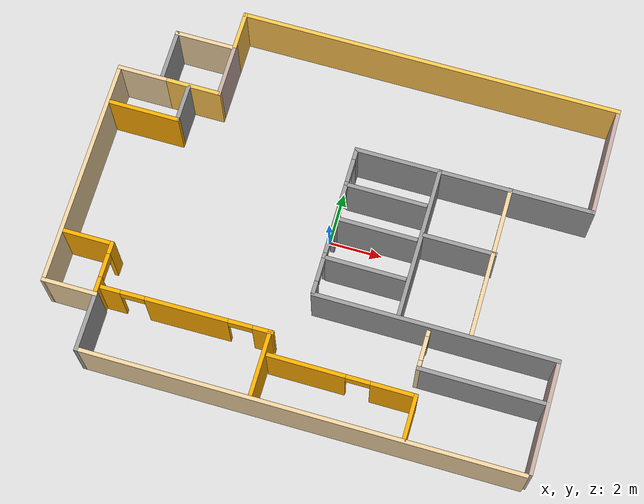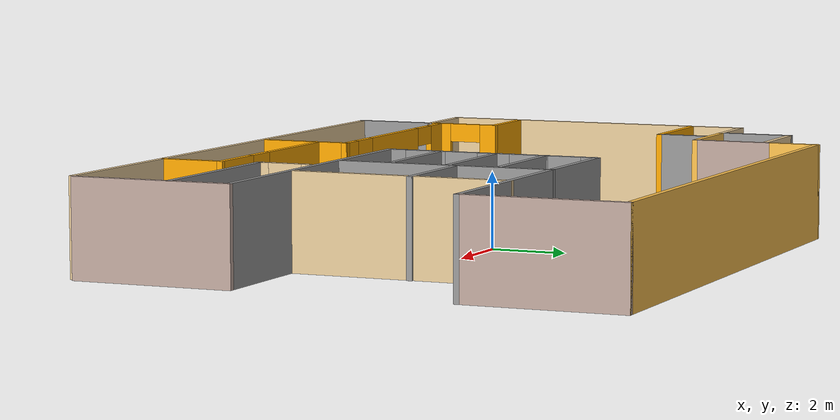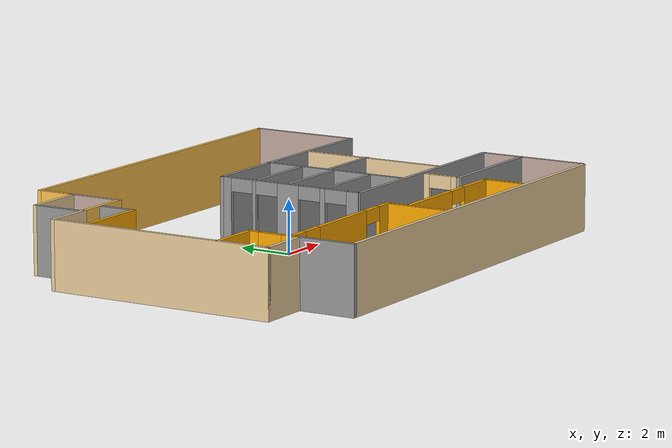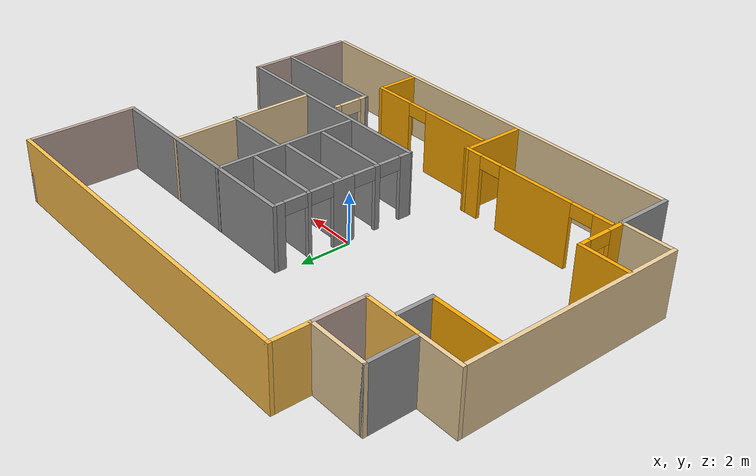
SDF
<?xml version='1.0'?>
<sdf version='1.6'>
  <model name='model'>
    <link name='Wall_100'>
      <pose frame=''>0.188472 0.1 0 0 0 -1.5708</pose>
      <self_collide>0</self_collide>
      <kinematic>0</kinematic>
      <visual name='Wall_100_Visual_8'>
        <pose frame=''>1.96449 0 2.25 0 -0 0</pose>
        <geometry>
          <box>
            <size>0.9 0.15 0.5</size>
          </box>
        </geometry>
        <material>
          <script>
            <uri>file://media/materials/scripts/gazebo.material</uri>
            <name>Gazebo/Grey</name>
          </script>
          <ambient>1 1 1 1</ambient>
          <shader type='pixel'/>
          <diffuse>0.7 0.7 0.7 1</diffuse>
          <specular>0.01 0.01 0.01 1</specular>
          <emissive>0 0 0 1</emissive>
        </material>
        <meta>
          <layer>0</layer>
        </meta>
        <transparency>0</transparency>
        <cast_shadows>1</cast_shadows>
      </visual>
      <visual name='Wall_100_Visual_0'>
        <pose frame=''>-2.66165 0 1.25 0 -0 0</pose>
        <geometry>
          <box>
            <size>0.47671 0.15 2.5</size>
          </box>
        </geometry>
        <material>
          <script>
            <uri>file://media/materials/scripts/gazebo.material</uri>
            <name>Gazebo/Grey</name>
          </script>
          <ambient>1 1 1 1</ambient>
          <shader type='pixel'/>
          <diffuse>0.7 0.7 0.7 1</diffuse>
          <specular>0.01 0.01 0.01 1</specular>
          <emissive>0 0 0 1</emissive>
        </material>
        <meta>
          <layer>0</layer>
        </meta>
        <transparency>0</transparency>
        <cast_shadows>1</cast_shadows>
      </visual>
      <visual name='Wall_100_Visual_1'>
        <pose frame=''>-1.4503 0 1.25 0 -0 0</pose>
        <geometry>
          <box>
            <size>0.145974 0.15 2.5</size>
          </box>
        </geometry>
        <material>
          <script>
            <uri>file://media/materials/scripts/gazebo.material</uri>
            <name>Gazebo/Grey</name>
          </script>
          <ambient>1 1 1 1</ambient>
          <shader type='pixel'/>
          <diffuse>0.7 0.7 0.7 1</diffuse>
          <specular>0.01 0.01 0.01 1</specular>
          <emissive>0 0 0 1</emissive>
        </material>
        <meta>
          <layer>0</layer>
        </meta>
        <transparency>0</transparency>
        <cast_shadows>1</cast_shadows>
      </visual>
      <visual name='Wall_100_Visual_2'>
        <pose frame=''>-0.035162 0 1.25 0 -0 0</pose>
        <geometry>
          <box>
            <size>0.884308 0.15 2.5</size>
          </box>
        </geometry>
        <material>
          <script>
            <uri>file://media/materials/scripts/gazebo.material</uri>
            <name>Gazebo/Grey</name>
          </script>
          <ambient>1 1 1 1</ambient>
          <shader type='pixel'/>
          <diffuse>0.7 0.7 0.7 1</diffuse>
          <specular>0.01 0.01 0.01 1</specular>
          <emissive>0 0 0 1</emissive>
        </material>
        <meta>
          <layer>0</layer>
        </meta>
        <transparency>0</transparency>
        <cast_shadows>1</cast_shadows>
      </visual>
      <visual name='Wall_100_Visual_3'>
        <pose frame=''>1.41074 0 1.25 0 -0 0</pose>
        <geometry>
          <box>
            <size>0.207502 0.15 2.5</size>
          </box>
        </geometry>
        <material>
          <script>
            <uri>file://media/materials/scripts/gazebo.material</uri>
            <name>Gazebo/Grey</name>
          </script>
          <ambient>1 1 1 1</ambient>
          <shader type='pixel'/>
          <diffuse>0.7 0.7 0.7 1</diffuse>
          <specular>0.01 0.01 0.01 1</specular>
          <emissive>0 0 0 1</emissive>
        </material>
        <meta>
          <layer>0</layer>
        </meta>
        <transparency>0</transparency>
        <cast_shadows>1</cast_shadows>
      </visual>
      <visual name='Wall_100_Visual_4'>
        <pose frame=''>2.65725 0 1.25 0 -0 0</pose>
        <geometry>
          <box>
            <size>0.485506 0.15 2.5</size>
          </box>
        </geometry>
        <material>
          <script>
            <uri>file://media/materials/scripts/gazebo.material</uri>
            <name>Gazebo/Grey</name>
          </script>
          <ambient>1 1 1 1</ambient>
          <shader type='pixel'/>
          <diffuse>0.7 0.7 0.7 1</diffuse>
          <specular>0.01 0.01 0.01 1</specular>
          <emissive>0 0 0 1</emissive>
        </material>
        <meta>
          <layer>0</layer>
        </meta>
        <transparency>0</transparency>
        <cast_shadows>1</cast_shadows>
      </visual>
      <visual name='Wall_100_Visual_5'>
        <pose frame=''>-1.97329 0 2.25 0 -0 0</pose>
        <geometry>
          <box>
            <size>0.9 0.15 0.5</size>
          </box>
        </geometry>
        <material>
          <script>
            <uri>file://media/materials/scripts/gazebo.material</uri>
            <name>Gazebo/Grey</name>
          </script>
          <ambient>1 1 1 1</ambient>
          <shader type='pixel'/>
          <diffuse>0.7 0.7 0.7 1</diffuse>
          <specular>0.01 0.01 0.01 1</specular>
          <emissive>0 0 0 1</emissive>
        </material>
        <meta>
          <layer>0</layer>
        </meta>
        <transparency>0</transparency>
        <cast_shadows>1</cast_shadows>
      </visual>
      <visual name='Wall_100_Visual_6'>
        <pose frame=''>-0.927316 0 2.25 0 -0 0</pose>
        <geometry>
          <box>
            <size>0.9 0.15 0.5</size>
          </box>
        </geometry>
        <material>
          <script>
            <uri>file://media/materials/scripts/gazebo.material</uri>
            <name>Gazebo/Grey</name>
          </script>
          <ambient>1 1 1 1</ambient>
          <shader type='pixel'/>
          <diffuse>0.7 0.7 0.7 1</diffuse>
          <specular>0.01 0.01 0.01 1</specular>
          <emissive>0 0 0 1</emissive>
        </material>
        <meta>
          <layer>0</layer>
        </meta>
        <transparency>0</transparency>
        <cast_shadows>1</cast_shadows>
      </visual>
      <visual name='Wall_100_Visual_7'>
        <pose frame=''>0.856992 0 2.25 0 -0 0</pose>
        <geometry>
          <box>
            <size>0.9 0.15 0.5</size>
          </box>
        </geometry>
        <material>
          <script>
            <uri>file://media/materials/scripts/gazebo.material</uri>
            <name>Gazebo/Grey</name>
          </script>
          <ambient>1 1 1 1</ambient>
          <shader type='pixel'/>
          <diffuse>0.7 0.7 0.7 1</diffuse>
          <specular>0.01 0.01 0.01 1</specular>
          <emissive>0 0 0 1</emissive>
        </material>
        <meta>
          <layer>0</layer>
        </meta>
        <transparency>0</transparency>
        <cast_shadows>1</cast_shadows>
      </visual>
      <collision name='Wall_100_Collision_0'>
        <laser_retro>0</laser_retro>
        <max_contacts>10</max_contacts>
        <pose frame=''>-2.66165 0 1.25 0 -0 0</pose>
        <geometry>
          <box>
            <size>0.47671 0.15 2.5</size>
          </box>
        </geometry>
        <surface>
          <friction>
            <ode>
              <mu>1</mu>
              <mu2>1</mu2>
              <fdir1>0 0 0</fdir1>
              <slip1>0</slip1>
              <slip2>0</slip2>
            </ode>
            <torsional>
              <coefficient>1</coefficient>
              <patch_radius>0</patch_radius>
              <surface_radius>0</surface_radius>
              <use_patch_radius>1</use_patch_radius>
              <ode>
                <slip>0</slip>
              </ode>
            </torsional>
          </friction>
          <bounce>
            <restitution_coefficient>0</restitution_coefficient>
            <threshold>1e+06</threshold>
          </bounce>
          <contact>
            <collide_without_contact>0</collide_without_contact>
            <collide_without_contact_bitmask>1</collide_without_contact_bitmask>
            <collide_bitmask>1</collide_bitmask>
            <ode>
              <soft_cfm>0</soft_cfm>
              <soft_erp>0.2</soft_erp>
              <kp>1e+13</kp>
              <kd>1</kd>
              <max_vel>0.01</max_vel>
              <min_depth>0</min_depth>
            </ode>
            <bullet>
              <split_impulse>1</split_impulse>
              <split_impulse_penetration_threshold>-0.01</split_impulse_penetration_threshold>
              <soft_cfm>0</soft_cfm>
              <soft_erp>0.2</soft_erp>
              <kp>1e+13</kp>
              <kd>1</kd>
            </bullet>
          </contact>
        </surface>
      </collision>
      <collision name='Wall_100_Collision_1'>
        <laser_retro>0</laser_retro>
        <max_contacts>10</max_contacts>
        <pose frame=''>-1.4503 0 1.25 0 -0 0</pose>
        <geometry>
          <box>
            <size>0.145974 0.15 2.5</size>
          </box>
        </geometry>
        <surface>
          <friction>
            <ode>
              <mu>1</mu>
              <mu2>1</mu2>
              <fdir1>0 0 0</fdir1>
              <slip1>0</slip1>
              <slip2>0</slip2>
            </ode>
            <torsional>
              <coefficient>1</coefficient>
              <patch_radius>0</patch_radius>
              <surface_radius>0</surface_radius>
              <use_patch_radius>1</use_patch_radius>
              <ode>
                <slip>0</slip>
              </ode>
            </torsional>
          </friction>
          <bounce>
            <restitution_coefficient>0</restitution_coefficient>
            <threshold>1e+06</threshold>
          </bounce>
          <contact>
            <collide_without_contact>0</collide_without_contact>
            <collide_without_contact_bitmask>1</collide_without_contact_bitmask>
            <collide_bitmask>1</collide_bitmask>
            <ode>
              <soft_cfm>0</soft_cfm>
              <soft_erp>0.2</soft_erp>
              <kp>1e+13</kp>
              <kd>1</kd>
              <max_vel>0.01</max_vel>
              <min_depth>0</min_depth>
            </ode>
            <bullet>
              <split_impulse>1</split_impulse>
              <split_impulse_penetration_threshold>-0.01</split_impulse_penetration_threshold>
              <soft_cfm>0</soft_cfm>
              <soft_erp>0.2</soft_erp>
              <kp>1e+13</kp>
              <kd>1</kd>
            </bullet>
          </contact>
        </surface>
      </collision>
      <collision name='Wall_100_Collision_2'>
        <laser_retro>0</laser_retro>
        <max_contacts>10</max_contacts>
        <pose frame=''>-0.035162 0 1.25 0 -0 0</pose>
        <geometry>
          <box>
            <size>0.884308 0.15 2.5</size>
          </box>
        </geometry>
        <surface>
          <friction>
            <ode>
              <mu>1</mu>
              <mu2>1</mu2>
              <fdir1>0 0 0</fdir1>
              <slip1>0</slip1>
              <slip2>0</slip2>
            </ode>
            <torsional>
              <coefficient>1</coefficient>
              <patch_radius>0</patch_radius>
              <surface_radius>0</surface_radius>
              <use_patch_radius>1</use_patch_radius>
              <ode>
                <slip>0</slip>
              </ode>
            </torsional>
          </friction>
          <bounce>
            <restitution_coefficient>0</restitution_coefficient>
            <threshold>1e+06</threshold>
          </bounce>
          <contact>
            <collide_without_contact>0</collide_without_contact>
            <collide_without_contact_bitmask>1</collide_without_contact_bitmask>
            <collide_bitmask>1</collide_bitmask>
            <ode>
              <soft_cfm>0</soft_cfm>
              <soft_erp>0.2</soft_erp>
              <kp>1e+13</kp>
              <kd>1</kd>
              <max_vel>0.01</max_vel>
              <min_depth>0</min_depth>
            </ode>
            <bullet>
              <split_impulse>1</split_impulse>
              <split_impulse_penetration_threshold>-0.01</split_impulse_penetration_threshold>
              <soft_cfm>0</soft_cfm>
              <soft_erp>0.2</soft_erp>
              <kp>1e+13</kp>
              <kd>1</kd>
            </bullet>
          </contact>
        </surface>
      </collision>
      <collision name='Wall_100_Collision_3'>
        <laser_retro>0</laser_retro>
        <max_contacts>10</max_contacts>
        <pose frame=''>1.41074 0 1.25 0 -0 0</pose>
        <geometry>
          <box>
            <size>0.207502 0.15 2.5</size>
          </box>
        </geometry>
        <surface>
          <friction>
            <ode>
              <mu>1</mu>
              <mu2>1</mu2>
              <fdir1>0 0 0</fdir1>
              <slip1>0</slip1>
              <slip2>0</slip2>
            </ode>
            <torsional>
              <coefficient>1</coefficient>
              <patch_radius>0</patch_radius>
              <surface_radius>0</surface_radius>
              <use_patch_radius>1</use_patch_radius>
              <ode>
                <slip>0</slip>
              </ode>
            </torsional>
          </friction>
          <bounce>
            <restitution_coefficient>0</restitution_coefficient>
            <threshold>1e+06</threshold>
          </bounce>
          <contact>
            <collide_without_contact>0</collide_without_contact>
            <collide_without_contact_bitmask>1</collide_without_contact_bitmask>
            <collide_bitmask>1</collide_bitmask>
            <ode>
              <soft_cfm>0</soft_cfm>
              <soft_erp>0.2</soft_erp>
              <kp>1e+13</kp>
              <kd>1</kd>
              <max_vel>0.01</max_vel>
              <min_depth>0</min_depth>
            </ode>
            <bullet>
              <split_impulse>1</split_impulse>
              <split_impulse_penetration_threshold>-0.01</split_impulse_penetration_threshold>
              <soft_cfm>0</soft_cfm>
              <soft_erp>0.2</soft_erp>
              <kp>1e+13</kp>
              <kd>1</kd>
            </bullet>
          </contact>
        </surface>
      </collision>
      <collision name='Wall_100_Collision_5'>
        <laser_retro>0</laser_retro>
        <max_contacts>10</max_contacts>
        <pose frame=''>-1.97329 0 2.25 0 -0 0</pose>
        <geometry>
          <box>
            <size>0.9 0.15 0.5</size>
          </box>
        </geometry>
        <surface>
          <friction>
            <ode>
              <mu>1</mu>
              <mu2>1</mu2>
              <fdir1>0 0 0</fdir1>
              <slip1>0</slip1>
              <slip2>0</slip2>
            </ode>
            <torsional>
              <coefficient>1</coefficient>
              <patch_radius>0</patch_radius>
              <surface_radius>0</surface_radius>
              <use_patch_radius>1</use_patch_radius>
              <ode>
                <slip>0</slip>
              </ode>
            </torsional>
          </friction>
          <bounce>
            <restitution_coefficient>0</restitution_coefficient>
            <threshold>1e+06</threshold>
          </bounce>
          <contact>
            <collide_without_contact>0</collide_without_contact>
            <collide_without_contact_bitmask>1</collide_without_contact_bitmask>
            <collide_bitmask>1</collide_bitmask>
            <ode>
              <soft_cfm>0</soft_cfm>
              <soft_erp>0.2</soft_erp>
              <kp>1e+13</kp>
              <kd>1</kd>
              <max_vel>0.01</max_vel>
              <min_depth>0</min_depth>
            </ode>
            <bullet>
              <split_impulse>1</split_impulse>
              <split_impulse_penetration_threshold>-0.01</split_impulse_penetration_threshold>
              <soft_cfm>0</soft_cfm>
              <soft_erp>0.2</soft_erp>
              <kp>1e+13</kp>
              <kd>1</kd>
            </bullet>
          </contact>
        </surface>
      </collision>
      <collision name='Wall_100_Collision_4'>
        <laser_retro>0</laser_retro>
        <max_contacts>10</max_contacts>
        <pose frame=''>2.65725 0 1.25 0 -0 0</pose>
        <geometry>
          <box>
            <size>0.485506 0.15 2.5</size>
          </box>
        </geometry>
        <surface>
          <friction>
            <ode>
              <mu>1</mu>
              <mu2>1</mu2>
              <fdir1>0 0 0</fdir1>
              <slip1>0</slip1>
              <slip2>0</slip2>
            </ode>
            <torsional>
              <coefficient>1</coefficient>
              <patch_radius>0</patch_radius>
              <surface_radius>0</surface_radius>
              <use_patch_radius>1</use_patch_radius>
              <ode>
                <slip>0</slip>
              </ode>
            </torsional>
          </friction>
          <bounce>
            <restitution_coefficient>0</restitution_coefficient>
            <threshold>1e+06</threshold>
          </bounce>
          <contact>
            <collide_without_contact>0</collide_without_contact>
            <collide_without_contact_bitmask>1</collide_without_contact_bitmask>
            <collide_bitmask>1</collide_bitmask>
            <ode>
              <soft_cfm>0</soft_cfm>
              <soft_erp>0.2</soft_erp>
              <kp>1e+13</kp>
              <kd>1</kd>
              <max_vel>0.01</max_vel>
              <min_depth>0</min_depth>
            </ode>
            <bullet>
              <split_impulse>1</split_impulse>
              <split_impulse_penetration_threshold>-0.01</split_impulse_penetration_threshold>
              <soft_cfm>0</soft_cfm>
              <soft_erp>0.2</soft_erp>
              <kp>1e+13</kp>
              <kd>1</kd>
            </bullet>
          </contact>
        </surface>
      </collision>
      <collision name='Wall_100_Collision_6'>
        <laser_retro>0</laser_retro>
        <max_contacts>10</max_contacts>
        <pose frame=''>-0.927316 0 2.25 0 -0 0</pose>
        <geometry>
          <box>
            <size>0.9 0.15 0.5</size>
          </box>
        </geometry>
        <surface>
          <friction>
            <ode>
              <mu>1</mu>
              <mu2>1</mu2>
              <fdir1>0 0 0</fdir1>
              <slip1>0</slip1>
              <slip2>0</slip2>
            </ode>
            <torsional>
              <coefficient>1</coefficient>
              <patch_radius>0</patch_radius>
              <surface_radius>0</surface_radius>
              <use_patch_radius>1</use_patch_radius>
              <ode>
                <slip>0</slip>
              </ode>
            </torsional>
          </friction>
          <bounce>
            <restitution_coefficient>0</restitution_coefficient>
            <threshold>1e+06</threshold>
          </bounce>
          <contact>
            <collide_without_contact>0</collide_without_contact>
            <collide_without_contact_bitmask>1</collide_without_contact_bitmask>
            <collide_bitmask>1</collide_bitmask>
            <ode>
              <soft_cfm>0</soft_cfm>
              <soft_erp>0.2</soft_erp>
              <kp>1e+13</kp>
              <kd>1</kd>
              <max_vel>0.01</max_vel>
              <min_depth>0</min_depth>
            </ode>
            <bullet>
              <split_impulse>1</split_impulse>
              <split_impulse_penetration_threshold>-0.01</split_impulse_penetration_threshold>
              <soft_cfm>0</soft_cfm>
              <soft_erp>0.2</soft_erp>
              <kp>1e+13</kp>
              <kd>1</kd>
            </bullet>
          </contact>
        </surface>
      </collision>
      <collision name='Wall_100_Collision_7'>
        <laser_retro>0</laser_retro>
        <max_contacts>10</max_contacts>
        <pose frame=''>0.856992 0 2.25 0 -0 0</pose>
        <geometry>
          <box>
            <size>0.9 0.15 0.5</size>
          </box>
        </geometry>
        <surface>
          <friction>
            <ode>
              <mu>1</mu>
              <mu2>1</mu2>
              <fdir1>0 0 0</fdir1>
              <slip1>0</slip1>
              <slip2>0</slip2>
            </ode>
            <torsional>
              <coefficient>1</coefficient>
              <patch_radius>0</patch_radius>
              <surface_radius>0</surface_radius>
              <use_patch_radius>1</use_patch_radius>
              <ode>
                <slip>0</slip>
              </ode>
            </torsional>
          </friction>
          <bounce>
            <restitution_coefficient>0</restitution_coefficient>
            <threshold>1e+06</threshold>
          </bounce>
          <contact>
            <collide_without_contact>0</collide_without_contact>
            <collide_without_contact_bitmask>1</collide_without_contact_bitmask>
            <collide_bitmask>1</collide_bitmask>
            <ode>
              <soft_cfm>0</soft_cfm>
              <soft_erp>0.2</soft_erp>
              <kp>1e+13</kp>
              <kd>1</kd>
              <max_vel>0.01</max_vel>
              <min_depth>0</min_depth>
            </ode>
            <bullet>
              <split_impulse>1</split_impulse>
              <split_impulse_penetration_threshold>-0.01</split_impulse_penetration_threshold>
              <soft_cfm>0</soft_cfm>
              <soft_erp>0.2</soft_erp>
              <kp>1e+13</kp>
              <kd>1</kd>
            </bullet>
          </contact>
        </surface>
      </collision>
      <collision name='Wall_100_Collision_8'>
        <laser_retro>0</laser_retro>
        <max_contacts>10</max_contacts>
        <pose frame=''>1.96449 0 2.25 0 -0 0</pose>
        <geometry>
          <box>
            <size>0.9 0.15 0.5</size>
          </box>
        </geometry>
        <surface>
          <friction>
            <ode>
              <mu>1</mu>
              <mu2>1</mu2>
              <fdir1>0 0 0</fdir1>
              <slip1>0</slip1>
              <slip2>0</slip2>
            </ode>
            <torsional>
              <coefficient>1</coefficient>
              <patch_radius>0</patch_radius>
              <surface_radius>0</surface_radius>
              <use_patch_radius>1</use_patch_radius>
              <ode>
                <slip>0</slip>
              </ode>
            </torsional>
          </friction>
          <bounce>
            <restitution_coefficient>0</restitution_coefficient>
            <threshold>1e+06</threshold>
          </bounce>
          <contact>
            <collide_without_contact>0</collide_without_contact>
            <collide_without_contact_bitmask>1</collide_without_contact_bitmask>
            <collide_bitmask>1</collide_bitmask>
            <ode>
              <soft_cfm>0</soft_cfm>
              <soft_erp>0.2</soft_erp>
              <kp>1e+13</kp>
              <kd>1</kd>
              <max_vel>0.01</max_vel>
              <min_depth>0</min_depth>
            </ode>
            <bullet>
              <split_impulse>1</split_impulse>
              <split_impulse_penetration_threshold>-0.01</split_impulse_penetration_threshold>
              <soft_cfm>0</soft_cfm>
              <soft_erp>0.2</soft_erp>
              <kp>1e+13</kp>
              <kd>1</kd>
            </bullet>
          </contact>
        </surface>
      </collision>
    </link>
    <link name='Wall_102'>
      <pose frame=''>1.73212 1.51954 0 0 -0 0</pose>
      <self_collide>0</self_collide>
      <kinematic>0</kinematic>
      <visual name='Wall_102_Visual'>
        <pose frame=''>0 0 1.25 0 -0 0</pose>
        <geometry>
          <box>
            <size>3 0.15 2.5</size>
          </box>
        </geometry>
        <material>
          <script>
            <uri>file://media/materials/scripts/gazebo.material</uri>
            <name>Gazebo/Grey</name>
          </script>
          <ambient>1 1 1 1</ambient>
          <shader type='pixel'/>
          <diffuse>0.7 0.7 0.7 1</diffuse>
          <specular>0.01 0.01 0.01 1</specular>
          <emissive>0 0 0 1</emissive>
        </material>
        <meta>
          <layer>0</layer>
        </meta>
        <transparency>0</transparency>
        <cast_shadows>1</cast_shadows>
      </visual>
      <collision name='Wall_102_Collision'>
        <laser_retro>0</laser_retro>
        <max_contacts>10</max_contacts>
        <pose frame=''>0 0 1.25 0 -0 0</pose>
        <geometry>
          <box>
            <size>3 0.15 2.5</size>
          </box>
        </geometry>
        <surface>
          <friction>
            <ode>
              <mu>1</mu>
              <mu2>1</mu2>
              <fdir1>0 0 0</fdir1>
              <slip1>0</slip1>
              <slip2>0</slip2>
            </ode>
            <torsional>
              <coefficient>1</coefficient>
              <patch_radius>0</patch_radius>
              <surface_radius>0</surface_radius>
              <use_patch_radius>1</use_patch_radius>
              <ode>
                <slip>0</slip>
              </ode>
            </torsional>
          </friction>
          <bounce>
            <restitution_coefficient>0</restitution_coefficient>
            <threshold>1e+06</threshold>
          </bounce>
          <contact>
            <collide_without_contact>0</collide_without_contact>
            <collide_without_contact_bitmask>1</collide_without_contact_bitmask>
            <collide_bitmask>1</collide_bitmask>
            <ode>
              <soft_cfm>0</soft_cfm>
              <soft_erp>0.2</soft_erp>
              <kp>1e+13</kp>
              <kd>1</kd>
              <max_vel>0.01</max_vel>
              <min_depth>0</min_depth>
            </ode>
            <bullet>
              <split_impulse>1</split_impulse>
              <split_impulse_penetration_threshold>-0.01</split_impulse_penetration_threshold>
              <soft_cfm>0</soft_cfm>
              <soft_erp>0.2</soft_erp>
              <kp>1e+13</kp>
              <kd>1</kd>
            </bullet>
          </contact>
        </surface>
      </collision>
    </link>
    <link name='Wall_104'>
      <pose frame=''>1.73212 0.165926 0 0 -0 0</pose>
      <self_collide>0</self_collide>
      <kinematic>0</kinematic>
      <visual name='Wall_104_Visual'>
        <pose frame=''>0 0 1.25 0 -0 0</pose>
        <geometry>
          <box>
            <size>3 0.15 2.5</size>
          </box>
        </geometry>
        <material>
          <script>
            <uri>file://media/materials/scripts/gazebo.material</uri>
            <name>Gazebo/Grey</name>
          </script>
          <ambient>1 1 1 1</ambient>
          <shader type='pixel'/>
          <diffuse>0.7 0.7 0.7 1</diffuse>
          <specular>0.01 0.01 0.01 1</specular>
          <emissive>0 0 0 1</emissive>
        </material>
        <meta>
          <layer>0</layer>
        </meta>
        <transparency>0</transparency>
        <cast_shadows>1</cast_shadows>
      </visual>
      <collision name='Wall_104_Collision'>
        <laser_retro>0</laser_retro>
        <max_contacts>10</max_contacts>
        <pose frame=''>0 0 1.25 0 -0 0</pose>
        <geometry>
          <box>
            <size>3 0.15 2.5</size>
          </box>
        </geometry>
        <surface>
          <friction>
            <ode>
              <mu>1</mu>
              <mu2>1</mu2>
              <fdir1>0 0 0</fdir1>
              <slip1>0</slip1>
              <slip2>0</slip2>
            </ode>
            <torsional>
              <coefficient>1</coefficient>
              <patch_radius>0</patch_radius>
              <surface_radius>0</surface_radius>
              <use_patch_radius>1</use_patch_radius>
              <ode>
                <slip>0</slip>
              </ode>
            </torsional>
          </friction>
          <bounce>
            <restitution_coefficient>0</restitution_coefficient>
            <threshold>1e+06</threshold>
          </bounce>
          <contact>
            <collide_without_contact>0</collide_without_contact>
            <collide_without_contact_bitmask>1</collide_without_contact_bitmask>
            <collide_bitmask>1</collide_bitmask>
            <ode>
              <soft_cfm>0</soft_cfm>
              <soft_erp>0.2</soft_erp>
              <kp>1e+13</kp>
              <kd>1</kd>
              <max_vel>0.01</max_vel>
              <min_depth>0</min_depth>
            </ode>
            <bullet>
              <split_impulse>1</split_impulse>
              <split_impulse_penetration_threshold>-0.01</split_impulse_penetration_threshold>
              <soft_cfm>0</soft_cfm>
              <soft_erp>0.2</soft_erp>
              <kp>1e+13</kp>
              <kd>1</kd>
            </bullet>
          </contact>
        </surface>
      </collision>
    </link>
    <link name='Wall_106'>
      <pose frame=''>1.73212 -1.37227 0 0 -0 0</pose>
      <self_collide>0</self_collide>
      <kinematic>0</kinematic>
      <visual name='Wall_106_Visual'>
        <pose frame=''>0 0 1.25 0 -0 0</pose>
        <geometry>
          <box>
            <size>3 0.15 2.5</size>
          </box>
        </geometry>
        <material>
          <script>
            <uri>file://media/materials/scripts/gazebo.material</uri>
            <name>Gazebo/Grey</name>
          </script>
          <ambient>1 1 1 1</ambient>
          <shader type='pixel'/>
          <diffuse>0.7 0.7 0.7 1</diffuse>
          <specular>0.01 0.01 0.01 1</specular>
          <emissive>0 0 0 1</emissive>
        </material>
        <meta>
          <layer>0</layer>
        </meta>
        <transparency>0</transparency>
        <cast_shadows>1</cast_shadows>
      </visual>
      <collision name='Wall_106_Collision'>
        <laser_retro>0</laser_retro>
        <max_contacts>10</max_contacts>
        <pose frame=''>0 0 1.25 0 -0 0</pose>
        <geometry>
          <box>
            <size>3 0.15 2.5</size>
          </box>
        </geometry>
        <surface>
          <friction>
            <ode>
              <mu>1</mu>
              <mu2>1</mu2>
              <fdir1>0 0 0</fdir1>
              <slip1>0</slip1>
              <slip2>0</slip2>
            </ode>
            <torsional>
              <coefficient>1</coefficient>
              <patch_radius>0</patch_radius>
              <surface_radius>0</surface_radius>
              <use_patch_radius>1</use_patch_radius>
              <ode>
                <slip>0</slip>
              </ode>
            </torsional>
          </friction>
          <bounce>
            <restitution_coefficient>0</restitution_coefficient>
            <threshold>1e+06</threshold>
          </bounce>
          <contact>
            <collide_without_contact>0</collide_without_contact>
            <collide_without_contact_bitmask>1</collide_without_contact_bitmask>
            <collide_bitmask>1</collide_bitmask>
            <ode>
              <soft_cfm>0</soft_cfm>
              <soft_erp>0.2</soft_erp>
              <kp>1e+13</kp>
              <kd>1</kd>
              <max_vel>0.01</max_vel>
              <min_depth>0</min_depth>
            </ode>
            <bullet>
              <split_impulse>1</split_impulse>
              <split_impulse_penetration_threshold>-0.01</split_impulse_penetration_threshold>
              <soft_cfm>0</soft_cfm>
              <soft_erp>0.2</soft_erp>
              <kp>1e+13</kp>
              <kd>1</kd>
            </bullet>
          </contact>
        </surface>
      </collision>
    </link>
    <link name='Wall_108'>
      <pose frame=''>-5.31153 6.35 0 0 0 -1.5708</pose>
      <self_collide>0</self_collide>
      <kinematic>0</kinematic>
      <visual name='Wall_108_Visual'>
        <pose frame=''>0 0 1.25 0 -0 0</pose>
        <geometry>
          <box>
            <size>1.5 0.15 2.5</size>
          </box>
        </geometry>
        <material>
          <script>
            <uri>file://media/materials/scripts/gazebo.material</uri>
            <name>Gazebo/Grey</name>
          </script>
          <ambient>1 0.764706 0.305882 1</ambient>
          <shader type='pixel'/>
          <diffuse>0.7 0.7 0.7 1</diffuse>
          <specular>0.01 0.01 0.01 1</specular>
          <emissive>0 0 0 1</emissive>
        </material>
        <meta>
          <layer>0</layer>
        </meta>
        <transparency>0</transparency>
        <cast_shadows>1</cast_shadows>
      </visual>
      <collision name='Wall_108_Collision'>
        <laser_retro>0</laser_retro>
        <max_contacts>10</max_contacts>
        <pose frame=''>0 0 1.25 0 -0 0</pose>
        <geometry>
          <box>
            <size>1.5 0.15 2.5</size>
          </box>
        </geometry>
        <surface>
          <friction>
            <ode>
              <mu>1</mu>
              <mu2>1</mu2>
              <fdir1>0 0 0</fdir1>
              <slip1>0</slip1>
              <slip2>0</slip2>
            </ode>
            <torsional>
              <coefficient>1</coefficient>
              <patch_radius>0</patch_radius>
              <surface_radius>0</surface_radius>
              <use_patch_radius>1</use_patch_radius>
              <ode>
                <slip>0</slip>
              </ode>
            </torsional>
          </friction>
          <bounce>
            <restitution_coefficient>0</restitution_coefficient>
            <threshold>1e+06</threshold>
          </bounce>
          <contact>
            <collide_without_contact>0</collide_without_contact>
            <collide_without_contact_bitmask>1</collide_without_contact_bitmask>
            <collide_bitmask>1</collide_bitmask>
            <ode>
              <soft_cfm>0</soft_cfm>
              <soft_erp>0.2</soft_erp>
              <kp>1e+13</kp>
              <kd>1</kd>
              <max_vel>0.01</max_vel>
              <min_depth>0</min_depth>
            </ode>
            <bullet>
              <split_impulse>1</split_impulse>
              <split_impulse_penetration_threshold>-0.01</split_impulse_penetration_threshold>
              <soft_cfm>0</soft_cfm>
              <soft_erp>0.2</soft_erp>
              <kp>1e+13</kp>
              <kd>1</kd>
            </bullet>
          </contact>
        </surface>
      </collision>
    </link>
    <link name='Wall_109'>
      <pose frame=''>-5.31153 4.675 0 0 0 -1.5708</pose>
      <self_collide>0</self_collide>
      <kinematic>0</kinematic>
      <visual name='Wall_109_Visual'>
        <pose frame=''>0 0 1.25 0 -0 0</pose>
        <geometry>
          <box>
            <size>2.15 0.15 2.5</size>
          </box>
        </geometry>
        <material>
          <script>
            <uri>file://media/materials/scripts/gazebo.material</uri>
            <name>Gazebo/Grey</name>
          </script>
          <ambient>0.760784 0.662745 0.627451 1</ambient>
          <shader type='pixel'/>
          <diffuse>0.7 0.7 0.7 1</diffuse>
          <specular>0.01 0.01 0.01 1</specular>
          <emissive>0 0 0 1</emissive>
        </material>
        <meta>
          <layer>0</layer>
        </meta>
        <transparency>0</transparency>
        <cast_shadows>1</cast_shadows>
      </visual>
      <collision name='Wall_109_Collision'>
        <laser_retro>0</laser_retro>
        <max_contacts>10</max_contacts>
        <pose frame=''>0 0 1.25 0 -0 0</pose>
        <geometry>
          <box>
            <size>2.15 0.15 2.5</size>
          </box>
        </geometry>
        <surface>
          <friction>
            <ode>
              <mu>1</mu>
              <mu2>1</mu2>
              <fdir1>0 0 0</fdir1>
              <slip1>0</slip1>
              <slip2>0</slip2>
            </ode>
            <torsional>
              <coefficient>1</coefficient>
              <patch_radius>0</patch_radius>
              <surface_radius>0</surface_radius>
              <use_patch_radius>1</use_patch_radius>
              <ode>
                <slip>0</slip>
              </ode>
            </torsional>
          </friction>
          <bounce>
            <restitution_coefficient>0</restitution_coefficient>
            <threshold>1e+06</threshold>
          </bounce>
          <contact>
            <collide_without_contact>0</collide_without_contact>
            <collide_without_contact_bitmask>1</collide_without_contact_bitmask>
            <collide_bitmask>1</collide_bitmask>
            <ode>
              <soft_cfm>0</soft_cfm>
              <soft_erp>0.2</soft_erp>
              <kp>1e+13</kp>
              <kd>1</kd>
              <max_vel>0.01</max_vel>
              <min_depth>0</min_depth>
            </ode>
            <bullet>
              <split_impulse>1</split_impulse>
              <split_impulse_penetration_threshold>-0.01</split_impulse_penetration_threshold>
              <soft_cfm>0</soft_cfm>
              <soft_erp>0.2</soft_erp>
              <kp>1e+13</kp>
              <kd>1</kd>
            </bullet>
          </contact>
        </surface>
      </collision>
    </link>
    <link name='Wall_113'>
      <pose frame=''>-6.36153 3.675 0 0 -0 3.14159</pose>
      <self_collide>0</self_collide>
      <kinematic>0</kinematic>
      <visual name='Wall_113_Visual'>
        <pose frame=''>0 0 1.25 0 -0 0</pose>
        <geometry>
          <box>
            <size>2.25 0.15 2.5</size>
          </box>
        </geometry>
        <material>
          <script>
            <uri>file://media/materials/scripts/gazebo.material</uri>
            <name>Gazebo/Grey</name>
          </script>
          <ambient>1 0.764706 0.305882 1</ambient>
          <shader type='pixel'/>
          <diffuse>0.7 0.7 0.7 1</diffuse>
          <specular>0.01 0.01 0.01 1</specular>
          <emissive>0 0 0 1</emissive>
        </material>
        <meta>
          <layer>0</layer>
        </meta>
        <transparency>0</transparency>
        <cast_shadows>1</cast_shadows>
      </visual>
      <collision name='Wall_113_Collision'>
        <laser_retro>0</laser_retro>
        <max_contacts>10</max_contacts>
        <pose frame=''>0 0 1.25 0 -0 0</pose>
        <geometry>
          <box>
            <size>2.25 0.15 2.5</size>
          </box>
        </geometry>
        <surface>
          <friction>
            <ode>
              <mu>1</mu>
              <mu2>1</mu2>
              <fdir1>0 0 0</fdir1>
              <slip1>0</slip1>
              <slip2>0</slip2>
            </ode>
            <torsional>
              <coefficient>1</coefficient>
              <patch_radius>0</patch_radius>
              <surface_radius>0</surface_radius>
              <use_patch_radius>1</use_patch_radius>
              <ode>
                <slip>0</slip>
              </ode>
            </torsional>
          </friction>
          <bounce>
            <restitution_coefficient>0</restitution_coefficient>
            <threshold>1e+06</threshold>
          </bounce>
          <contact>
            <collide_without_contact>0</collide_without_contact>
            <collide_without_contact_bitmask>1</collide_without_contact_bitmask>
            <collide_bitmask>1</collide_bitmask>
            <ode>
              <soft_cfm>0</soft_cfm>
              <soft_erp>0.2</soft_erp>
              <kp>1e+13</kp>
              <kd>1</kd>
              <max_vel>0.01</max_vel>
              <min_depth>0</min_depth>
            </ode>
            <bullet>
              <split_impulse>1</split_impulse>
              <split_impulse_penetration_threshold>-0.01</split_impulse_penetration_threshold>
              <soft_cfm>0</soft_cfm>
              <soft_erp>0.2</soft_erp>
              <kp>1e+13</kp>
              <kd>1</kd>
            </bullet>
          </contact>
        </surface>
      </collision>
    </link>
    <link name='Wall_114'>
      <pose frame=''>-8.28653 3.675 0 0 -0 3.14159</pose>
      <self_collide>0</self_collide>
      <kinematic>0</kinematic>
      <visual name='Wall_114_Visual'>
        <pose frame=''>0 0 1.25 0 -0 0</pose>
        <geometry>
          <box>
            <size>1.9 0.15 2.5</size>
          </box>
        </geometry>
        <material>
          <script>
            <uri>file://media/materials/scripts/gazebo.material</uri>
            <name>Gazebo/Grey</name>
          </script>
          <ambient>0.921569 0.807843 0.615686 1</ambient>
          <shader type='pixel'/>
          <diffuse>0.7 0.7 0.7 1</diffuse>
          <specular>0.01 0.01 0.01 1</specular>
          <emissive>0 0 0 1</emissive>
        </material>
        <meta>
          <layer>0</layer>
        </meta>
        <transparency>0</transparency>
        <cast_shadows>1</cast_shadows>
      </visual>
      <collision name='Wall_114_Collision'>
        <laser_retro>0</laser_retro>
        <max_contacts>10</max_contacts>
        <pose frame=''>0 0 1.25 0 -0 0</pose>
        <geometry>
          <box>
            <size>1.9 0.15 2.5</size>
          </box>
        </geometry>
        <surface>
          <friction>
            <ode>
              <mu>1</mu>
              <mu2>1</mu2>
              <fdir1>0 0 0</fdir1>
              <slip1>0</slip1>
              <slip2>0</slip2>
            </ode>
            <torsional>
              <coefficient>1</coefficient>
              <patch_radius>0</patch_radius>
              <surface_radius>0</surface_radius>
              <use_patch_radius>1</use_patch_radius>
              <ode>
                <slip>0</slip>
              </ode>
            </torsional>
          </friction>
          <bounce>
            <restitution_coefficient>0</restitution_coefficient>
            <threshold>1e+06</threshold>
          </bounce>
          <contact>
            <collide_without_contact>0</collide_without_contact>
            <collide_without_contact_bitmask>1</collide_without_contact_bitmask>
            <collide_bitmask>1</collide_bitmask>
            <ode>
              <soft_cfm>0</soft_cfm>
              <soft_erp>0.2</soft_erp>
              <kp>1e+13</kp>
              <kd>1</kd>
              <max_vel>0.01</max_vel>
              <min_depth>0</min_depth>
            </ode>
            <bullet>
              <split_impulse>1</split_impulse>
              <split_impulse_penetration_threshold>-0.01</split_impulse_penetration_threshold>
              <soft_cfm>0</soft_cfm>
              <soft_erp>0.2</soft_erp>
              <kp>1e+13</kp>
              <kd>1</kd>
            </bullet>
          </contact>
        </surface>
      </collision>
    </link>
    <link name='Wall_13'>
      <pose frame=''>1.86347 7.025 0 0 -0 0</pose>
      <self_collide>0</self_collide>
      <kinematic>0</kinematic>
      <visual name='Wall_13_Visual'>
        <pose frame=''>0 0 1.25 0 -0 0</pose>
        <geometry>
          <box>
            <size>14.5 0.15 2.5</size>
          </box>
        </geometry>
        <material>
          <script>
            <uri>file://media/materials/scripts/gazebo.material</uri>
            <name>Gazebo/Grey</name>
          </script>
          <ambient>1 0.764706 0.305882 1</ambient>
          <shader type='pixel'/>
          <diffuse>0.7 0.7 0.7 1</diffuse>
          <specular>0.01 0.01 0.01 1</specular>
          <emissive>0 0 0 1</emissive>
        </material>
        <meta>
          <layer>0</layer>
        </meta>
        <transparency>0</transparency>
        <cast_shadows>1</cast_shadows>
      </visual>
      <collision name='Wall_13_Collision'>
        <laser_retro>0</laser_retro>
        <max_contacts>10</max_contacts>
        <pose frame=''>0 0 1.25 0 -0 0</pose>
        <geometry>
          <box>
            <size>14.5 0.15 2.5</size>
          </box>
        </geometry>
        <surface>
          <friction>
            <ode>
              <mu>1</mu>
              <mu2>1</mu2>
              <fdir1>0 0 0</fdir1>
              <slip1>0</slip1>
              <slip2>0</slip2>
            </ode>
            <torsional>
              <coefficient>1</coefficient>
              <patch_radius>0</patch_radius>
              <surface_radius>0</surface_radius>
              <use_patch_radius>1</use_patch_radius>
              <ode>
                <slip>0</slip>
              </ode>
            </torsional>
          </friction>
          <bounce>
            <restitution_coefficient>0</restitution_coefficient>
            <threshold>1e+06</threshold>
          </bounce>
          <contact>
            <collide_without_contact>0</collide_without_contact>
            <collide_without_contact_bitmask>1</collide_without_contact_bitmask>
            <collide_bitmask>1</collide_bitmask>
            <ode>
              <soft_cfm>0</soft_cfm>
              <soft_erp>0.2</soft_erp>
              <kp>1e+13</kp>
              <kd>1</kd>
              <max_vel>0.01</max_vel>
              <min_depth>0</min_depth>
            </ode>
            <bullet>
              <split_impulse>1</split_impulse>
              <split_impulse_penetration_threshold>-0.01</split_impulse_penetration_threshold>
              <soft_cfm>0</soft_cfm>
              <soft_erp>0.2</soft_erp>
              <kp>1e+13</kp>
              <kd>1</kd>
            </bullet>
          </contact>
        </surface>
      </collision>
    </link>
    <link name='Wall_15'>
      <pose frame=''>-7.53411 4.67076 0 0 -0 1.5708</pose>
      <self_collide>0</self_collide>
      <kinematic>0</kinematic>
      <visual name='Wall_15_Visual'>
        <pose frame=''>0 0 1.25 0 -0 0</pose>
        <geometry>
          <box>
            <size>2 0.15 2.5</size>
          </box>
        </geometry>
        <material>
          <script>
            <uri>file://media/materials/scripts/gazebo.material</uri>
            <name>Gazebo/Grey</name>
          </script>
          <ambient>1 1 1 1</ambient>
          <shader type='pixel'/>
          <diffuse>0.7 0.7 0.7 1</diffuse>
          <specular>0.01 0.01 0.01 1</specular>
          <emissive>0 0 0 1</emissive>
        </material>
        <meta>
          <layer>0</layer>
        </meta>
        <transparency>0</transparency>
        <cast_shadows>1</cast_shadows>
      </visual>
      <collision name='Wall_15_Collision'>
        <laser_retro>0</laser_retro>
        <max_contacts>10</max_contacts>
        <pose frame=''>0 0 1.25 0 -0 0</pose>
        <geometry>
          <box>
            <size>2 0.15 2.5</size>
          </box>
        </geometry>
        <surface>
          <friction>
            <ode>
              <mu>1</mu>
              <mu2>1</mu2>
              <fdir1>0 0 0</fdir1>
              <slip1>0</slip1>
              <slip2>0</slip2>
            </ode>
            <torsional>
              <coefficient>1</coefficient>
              <patch_radius>0</patch_radius>
              <surface_radius>0</surface_radius>
              <use_patch_radius>1</use_patch_radius>
              <ode>
                <slip>0</slip>
              </ode>
            </torsional>
          </friction>
          <bounce>
            <restitution_coefficient>0</restitution_coefficient>
            <threshold>1e+06</threshold>
          </bounce>
          <contact>
            <collide_without_contact>0</collide_without_contact>
            <collide_without_contact_bitmask>1</collide_without_contact_bitmask>
            <collide_bitmask>1</collide_bitmask>
            <ode>
              <soft_cfm>0</soft_cfm>
              <soft_erp>0.2</soft_erp>
              <kp>1e+13</kp>
              <kd>1</kd>
              <max_vel>0.01</max_vel>
              <min_depth>0</min_depth>
            </ode>
            <bullet>
              <split_impulse>1</split_impulse>
              <split_impulse_penetration_threshold>-0.01</split_impulse_penetration_threshold>
              <soft_cfm>0</soft_cfm>
              <soft_erp>0.2</soft_erp>
              <kp>1e+13</kp>
              <kd>1</kd>
            </bullet>
          </contact>
        </surface>
      </collision>
    </link>
    <link name='Wall_16'>
      <pose frame=''>-6.48412 5.59576 0 0 -0 0</pose>
      <self_collide>0</self_collide>
      <kinematic>0</kinematic>
      <visual name='Wall_16_Visual'>
        <pose frame=''>0 0 1.25 0 -0 0</pose>
        <geometry>
          <box>
            <size>2.25 0.15 2.5</size>
          </box>
        </geometry>
        <material>
          <script>
            <uri>file://media/materials/scripts/gazebo.material</uri>
            <name>Gazebo/Grey</name>
          </script>
          <ambient>0.921569 0.807843 0.615686 1</ambient>
          <shader type='pixel'/>
          <diffuse>0.7 0.7 0.7 1</diffuse>
          <specular>0.01 0.01 0.01 1</specular>
          <emissive>0 0 0 1</emissive>
        </material>
        <meta>
          <layer>0</layer>
        </meta>
        <transparency>0</transparency>
        <cast_shadows>1</cast_shadows>
      </visual>
      <collision name='Wall_16_Collision'>
        <laser_retro>0</laser_retro>
        <max_contacts>10</max_contacts>
        <pose frame=''>0 0 1.25 0 -0 0</pose>
        <geometry>
          <box>
            <size>2.25 0.15 2.5</size>
          </box>
        </geometry>
        <surface>
          <friction>
            <ode>
              <mu>1</mu>
              <mu2>1</mu2>
              <fdir1>0 0 0</fdir1>
              <slip1>0</slip1>
              <slip2>0</slip2>
            </ode>
            <torsional>
              <coefficient>1</coefficient>
              <patch_radius>0</patch_radius>
              <surface_radius>0</surface_radius>
              <use_patch_radius>1</use_patch_radius>
              <ode>
                <slip>0</slip>
              </ode>
            </torsional>
          </friction>
          <bounce>
            <restitution_coefficient>0</restitution_coefficient>
            <threshold>1e+06</threshold>
          </bounce>
          <contact>
            <collide_without_contact>0</collide_without_contact>
            <collide_without_contact_bitmask>1</collide_without_contact_bitmask>
            <collide_bitmask>1</collide_bitmask>
            <ode>
              <soft_cfm>0</soft_cfm>
              <soft_erp>0.2</soft_erp>
              <kp>1e+13</kp>
              <kd>1</kd>
              <max_vel>0.01</max_vel>
              <min_depth>0</min_depth>
            </ode>
            <bullet>
              <split_impulse>1</split_impulse>
              <split_impulse_penetration_threshold>-0.01</split_impulse_penetration_threshold>
              <soft_cfm>0</soft_cfm>
              <soft_erp>0.2</soft_erp>
              <kp>1e+13</kp>
              <kd>1</kd>
            </bullet>
          </contact>
        </surface>
      </collision>
    </link>
    <link name='Wall_18'>
      <pose frame=''>-6.47276 2.92924 0 0 0 -1.5708</pose>
      <self_collide>0</self_collide>
      <kinematic>0</kinematic>
      <visual name='Wall_18_Visual'>
        <pose frame=''>0 0 1.25 0 -0 0</pose>
        <geometry>
          <box>
            <size>1.5 0.15 2.5</size>
          </box>
        </geometry>
        <material>
          <script>
            <uri>file://media/materials/scripts/gazebo.material</uri>
            <name>Gazebo/Grey</name>
          </script>
          <ambient>1 1 1 1</ambient>
          <shader type='pixel'/>
          <diffuse>0.7 0.7 0.7 1</diffuse>
          <specular>0.01 0.01 0.01 1</specular>
          <emissive>0 0 0 1</emissive>
        </material>
        <meta>
          <layer>0</layer>
        </meta>
        <transparency>0</transparency>
        <cast_shadows>1</cast_shadows>
      </visual>
      <collision name='Wall_18_Collision'>
        <laser_retro>0</laser_retro>
        <max_contacts>10</max_contacts>
        <pose frame=''>0 0 1.25 0 -0 0</pose>
        <geometry>
          <box>
            <size>1.5 0.15 2.5</size>
          </box>
        </geometry>
        <surface>
          <friction>
            <ode>
              <mu>1</mu>
              <mu2>1</mu2>
              <fdir1>0 0 0</fdir1>
              <slip1>0</slip1>
              <slip2>0</slip2>
            </ode>
            <torsional>
              <coefficient>1</coefficient>
              <patch_radius>0</patch_radius>
              <surface_radius>0</surface_radius>
              <use_patch_radius>1</use_patch_radius>
              <ode>
                <slip>0</slip>
              </ode>
            </torsional>
          </friction>
          <bounce>
            <restitution_coefficient>0</restitution_coefficient>
            <threshold>1e+06</threshold>
          </bounce>
          <contact>
            <collide_without_contact>0</collide_without_contact>
            <collide_without_contact_bitmask>1</collide_without_contact_bitmask>
            <collide_bitmask>1</collide_bitmask>
            <ode>
              <soft_cfm>0</soft_cfm>
              <soft_erp>0.2</soft_erp>
              <kp>1e+13</kp>
              <kd>1</kd>
              <max_vel>0.01</max_vel>
              <min_depth>0</min_depth>
            </ode>
            <bullet>
              <split_impulse>1</split_impulse>
              <split_impulse_penetration_threshold>-0.01</split_impulse_penetration_threshold>
              <soft_cfm>0</soft_cfm>
              <soft_erp>0.2</soft_erp>
              <kp>1e+13</kp>
              <kd>1</kd>
            </bullet>
          </contact>
        </surface>
      </collision>
    </link>
    <link name='Wall_19'>
      <pose frame=''>-7.74776 2.25424 0 0 -0 3.14159</pose>
      <self_collide>0</self_collide>
      <kinematic>0</kinematic>
      <visual name='Wall_19_Visual'>
        <pose frame=''>0 0 1.25 0 -0 0</pose>
        <geometry>
          <box>
            <size>2.7 0.15 2.5</size>
          </box>
        </geometry>
        <material>
          <script>
            <uri>file://media/materials/scripts/gazebo.material</uri>
            <name>Gazebo/Grey</name>
          </script>
          <ambient>1 0.666667 0 1</ambient>
          <shader type='pixel'/>
          <diffuse>0.7 0.7 0.7 1</diffuse>
          <specular>0.01 0.01 0.01 1</specular>
          <emissive>0 0 0 1</emissive>
        </material>
        <meta>
          <layer>0</layer>
        </meta>
        <transparency>0</transparency>
        <cast_shadows>1</cast_shadows>
      </visual>
      <collision name='Wall_19_Collision'>
        <laser_retro>0</laser_retro>
        <max_contacts>10</max_contacts>
        <pose frame=''>0 0 1.25 0 -0 0</pose>
        <geometry>
          <box>
            <size>2.7 0.15 2.5</size>
          </box>
        </geometry>
        <surface>
          <friction>
            <ode>
              <mu>1</mu>
              <mu2>1</mu2>
              <fdir1>0 0 0</fdir1>
              <slip1>0</slip1>
              <slip2>0</slip2>
            </ode>
            <torsional>
              <coefficient>1</coefficient>
              <patch_radius>0</patch_radius>
              <surface_radius>0</surface_radius>
              <use_patch_radius>1</use_patch_radius>
              <ode>
                <slip>0</slip>
              </ode>
            </torsional>
          </friction>
          <bounce>
            <restitution_coefficient>0</restitution_coefficient>
            <threshold>1e+06</threshold>
          </bounce>
          <contact>
            <collide_without_contact>0</collide_without_contact>
            <collide_without_contact_bitmask>1</collide_without_contact_bitmask>
            <collide_bitmask>1</collide_bitmask>
            <ode>
              <soft_cfm>0</soft_cfm>
              <soft_erp>0.2</soft_erp>
              <kp>1e+13</kp>
              <kd>1</kd>
              <max_vel>0.01</max_vel>
              <min_depth>0</min_depth>
            </ode>
            <bullet>
              <split_impulse>1</split_impulse>
              <split_impulse_penetration_threshold>-0.01</split_impulse_penetration_threshold>
              <soft_cfm>0</soft_cfm>
              <soft_erp>0.2</soft_erp>
              <kp>1e+13</kp>
              <kd>1</kd>
            </bullet>
          </contact>
        </surface>
      </collision>
    </link>
    <link name='Wall_2'>
      <pose frame=''>-9.16153 -0.625 0 0 0 -1.5708</pose>
      <self_collide>0</self_collide>
      <kinematic>0</kinematic>
      <visual name='Wall_2_Visual'>
        <pose frame=''>0 0 1.25 0 -0 0</pose>
        <geometry>
          <box>
            <size>8.75 0.15 2.5</size>
          </box>
        </geometry>
        <material>
          <script>
            <uri>file://media/materials/scripts/gazebo.material</uri>
            <name>Gazebo/Grey</name>
          </script>
          <ambient>0.921569 0.807843 0.615686 1</ambient>
          <shader type='pixel'/>
          <diffuse>0.7 0.7 0.7 1</diffuse>
          <specular>0.01 0.01 0.01 1</specular>
          <emissive>0 0 0 1</emissive>
        </material>
        <meta>
          <layer>0</layer>
        </meta>
        <transparency>0</transparency>
        <cast_shadows>1</cast_shadows>
      </visual>
      <collision name='Wall_2_Collision'>
        <laser_retro>0</laser_retro>
        <max_contacts>10</max_contacts>
        <pose frame=''>0 0 1.25 0 -0 0</pose>
        <geometry>
          <box>
            <size>8.75 0.15 2.5</size>
          </box>
        </geometry>
        <surface>
          <friction>
            <ode>
              <mu>1</mu>
              <mu2>1</mu2>
              <fdir1>0 0 0</fdir1>
              <slip1>0</slip1>
              <slip2>0</slip2>
            </ode>
            <torsional>
              <coefficient>1</coefficient>
              <patch_radius>0</patch_radius>
              <surface_radius>0</surface_radius>
              <use_patch_radius>1</use_patch_radius>
              <ode>
                <slip>0</slip>
              </ode>
            </torsional>
          </friction>
          <bounce>
            <restitution_coefficient>0</restitution_coefficient>
            <threshold>1e+06</threshold>
          </bounce>
          <contact>
            <collide_without_contact>0</collide_without_contact>
            <collide_without_contact_bitmask>1</collide_without_contact_bitmask>
            <collide_bitmask>1</collide_bitmask>
            <ode>
              <soft_cfm>0</soft_cfm>
              <soft_erp>0.2</soft_erp>
              <kp>1e+13</kp>
              <kd>1</kd>
              <max_vel>0.01</max_vel>
              <min_depth>0</min_depth>
            </ode>
            <bullet>
              <split_impulse>1</split_impulse>
              <split_impulse_penetration_threshold>-0.01</split_impulse_penetration_threshold>
              <soft_cfm>0</soft_cfm>
              <soft_erp>0.2</soft_erp>
              <kp>1e+13</kp>
              <kd>1</kd>
            </bullet>
          </contact>
        </surface>
      </collision>
    </link>
    <link name='Wall_21'>
      <pose frame=''>-8.16577 -2.97616 0 0 -0 0</pose>
      <self_collide>0</self_collide>
      <kinematic>0</kinematic>
      <visual name='Wall_21_Visual'>
        <pose frame=''>0 0 1.25 0 -0 0</pose>
        <geometry>
          <box>
            <size>2 0.15 2.5</size>
          </box>
        </geometry>
        <material>
          <script>
            <uri>file://media/materials/scripts/gazebo.material</uri>
            <name>Gazebo/Grey</name>
          </script>
          <ambient>1 0.666667 0 1</ambient>
          <shader type='pixel'/>
          <diffuse>0.7 0.7 0.7 1</diffuse>
          <specular>0.01 0.01 0.01 1</specular>
          <emissive>0 0 0 1</emissive>
        </material>
        <meta>
          <layer>0</layer>
        </meta>
        <transparency>0</transparency>
        <cast_shadows>1</cast_shadows>
      </visual>
      <collision name='Wall_21_Collision'>
        <laser_retro>0</laser_retro>
        <max_contacts>10</max_contacts>
        <pose frame=''>0 0 1.25 0 -0 0</pose>
        <geometry>
          <box>
            <size>2 0.15 2.5</size>
          </box>
        </geometry>
        <surface>
          <friction>
            <ode>
              <mu>1</mu>
              <mu2>1</mu2>
              <fdir1>0 0 0</fdir1>
              <slip1>0</slip1>
              <slip2>0</slip2>
            </ode>
            <torsional>
              <coefficient>1</coefficient>
              <patch_radius>0</patch_radius>
              <surface_radius>0</surface_radius>
              <use_patch_radius>1</use_patch_radius>
              <ode>
                <slip>0</slip>
              </ode>
            </torsional>
          </friction>
          <bounce>
            <restitution_coefficient>0</restitution_coefficient>
            <threshold>1e+06</threshold>
          </bounce>
          <contact>
            <collide_without_contact>0</collide_without_contact>
            <collide_without_contact_bitmask>1</collide_without_contact_bitmask>
            <collide_bitmask>1</collide_bitmask>
            <ode>
              <soft_cfm>0</soft_cfm>
              <soft_erp>0.2</soft_erp>
              <kp>1e+13</kp>
              <kd>1</kd>
              <max_vel>0.01</max_vel>
              <min_depth>0</min_depth>
            </ode>
            <bullet>
              <split_impulse>1</split_impulse>
              <split_impulse_penetration_threshold>-0.01</split_impulse_penetration_threshold>
              <soft_cfm>0</soft_cfm>
              <soft_erp>0.2</soft_erp>
              <kp>1e+13</kp>
              <kd>1</kd>
            </bullet>
          </contact>
        </surface>
      </collision>
    </link>
    <link name='Wall_24'>
      <pose frame=''>9.03847 4.975 0 0 0 -1.5708</pose>
      <self_collide>0</self_collide>
      <kinematic>0</kinematic>
      <visual name='Wall_24_Visual'>
        <pose frame=''>0 0 1.25 0 -0 0</pose>
        <geometry>
          <box>
            <size>4.25 0.15 2.5</size>
          </box>
        </geometry>
        <material>
          <script>
            <uri>file://media/materials/scripts/gazebo.material</uri>
            <name>Gazebo/Grey</name>
          </script>
          <ambient>0.760784 0.662745 0.627451 1</ambient>
          <shader type='pixel'/>
          <diffuse>0.7 0.7 0.7 1</diffuse>
          <specular>0.01 0.01 0.01 1</specular>
          <emissive>0 0 0 1</emissive>
        </material>
        <meta>
          <layer>0</layer>
        </meta>
        <transparency>0</transparency>
        <cast_shadows>1</cast_shadows>
      </visual>
      <collision name='Wall_24_Collision'>
        <laser_retro>0</laser_retro>
        <max_contacts>10</max_contacts>
        <pose frame=''>0 0 1.25 0 -0 0</pose>
        <geometry>
          <box>
            <size>4.25 0.15 2.5</size>
          </box>
        </geometry>
        <surface>
          <friction>
            <ode>
              <mu>1</mu>
              <mu2>1</mu2>
              <fdir1>0 0 0</fdir1>
              <slip1>0</slip1>
              <slip2>0</slip2>
            </ode>
            <torsional>
              <coefficient>1</coefficient>
              <patch_radius>0</patch_radius>
              <surface_radius>0</surface_radius>
              <use_patch_radius>1</use_patch_radius>
              <ode>
                <slip>0</slip>
              </ode>
            </torsional>
          </friction>
          <bounce>
            <restitution_coefficient>0</restitution_coefficient>
            <threshold>1e+06</threshold>
          </bounce>
          <contact>
            <collide_without_contact>0</collide_without_contact>
            <collide_without_contact_bitmask>1</collide_without_contact_bitmask>
            <collide_bitmask>1</collide_bitmask>
            <ode>
              <soft_cfm>0</soft_cfm>
              <soft_erp>0.2</soft_erp>
              <kp>1e+13</kp>
              <kd>1</kd>
              <max_vel>0.01</max_vel>
              <min_depth>0</min_depth>
            </ode>
            <bullet>
              <split_impulse>1</split_impulse>
              <split_impulse_penetration_threshold>-0.01</split_impulse_penetration_threshold>
              <soft_cfm>0</soft_cfm>
              <soft_erp>0.2</soft_erp>
              <kp>1e+13</kp>
              <kd>1</kd>
            </bullet>
          </contact>
        </surface>
      </collision>
    </link>
    <link name='Wall_26'>
      <pose frame=''>4.61347 2.925 0 0 -0 3.14159</pose>
      <self_collide>0</self_collide>
      <kinematic>0</kinematic>
      <visual name='Wall_26_Visual'>
        <pose frame=''>0 0 1.25 0 -0 0</pose>
        <geometry>
          <box>
            <size>9 0.15 2.5</size>
          </box>
        </geometry>
        <material>
          <script>
            <uri>file://media/materials/scripts/gazebo.material</uri>
            <name>Gazebo/Grey</name>
          </script>
          <ambient>1 1 1 1</ambient>
          <shader type='pixel'/>
          <diffuse>0.7 0.7 0.7 1</diffuse>
          <specular>0.01 0.01 0.01 1</specular>
          <emissive>0 0 0 1</emissive>
        </material>
        <meta>
          <layer>0</layer>
        </meta>
        <transparency>0</transparency>
        <cast_shadows>1</cast_shadows>
      </visual>
      <collision name='Wall_26_Collision'>
        <laser_retro>0</laser_retro>
        <max_contacts>10</max_contacts>
        <pose frame=''>0 0 1.25 0 -0 0</pose>
        <geometry>
          <box>
            <size>9 0.15 2.5</size>
          </box>
        </geometry>
        <surface>
          <friction>
            <ode>
              <mu>1</mu>
              <mu2>1</mu2>
              <fdir1>0 0 0</fdir1>
              <slip1>0</slip1>
              <slip2>0</slip2>
            </ode>
            <torsional>
              <coefficient>1</coefficient>
              <patch_radius>0</patch_radius>
              <surface_radius>0</surface_radius>
              <use_patch_radius>1</use_patch_radius>
              <ode>
                <slip>0</slip>
              </ode>
            </torsional>
          </friction>
          <bounce>
            <restitution_coefficient>0</restitution_coefficient>
            <threshold>1e+06</threshold>
          </bounce>
          <contact>
            <collide_without_contact>0</collide_without_contact>
            <collide_without_contact_bitmask>1</collide_without_contact_bitmask>
            <collide_bitmask>1</collide_bitmask>
            <ode>
              <soft_cfm>0</soft_cfm>
              <soft_erp>0.2</soft_erp>
              <kp>1e+13</kp>
              <kd>1</kd>
              <max_vel>0.01</max_vel>
              <min_depth>0</min_depth>
            </ode>
            <bullet>
              <split_impulse>1</split_impulse>
              <split_impulse_penetration_threshold>-0.01</split_impulse_penetration_threshold>
              <soft_cfm>0</soft_cfm>
              <soft_erp>0.2</soft_erp>
              <kp>1e+13</kp>
              <kd>1</kd>
            </bullet>
          </contact>
        </surface>
      </collision>
    </link>
    <link name='Wall_31'>
      <pose frame=''>4.68653 -2.80194 0 0 -0 3.14159</pose>
      <self_collide>0</self_collide>
      <kinematic>0</kinematic>
      <visual name='Wall_31_Visual'>
        <pose frame=''>0 0 1.25 0 -0 0</pose>
        <geometry>
          <box>
            <size>9.1 0.15 2.5</size>
          </box>
        </geometry>
        <material>
          <script>
            <uri>file://media/materials/scripts/gazebo.material</uri>
            <name>Gazebo/Grey</name>
          </script>
          <ambient>1 1 1 1</ambient>
          <shader type='pixel'/>
          <diffuse>0.7 0.7 0.7 1</diffuse>
          <specular>0.01 0.01 0.01 1</specular>
          <emissive>0 0 0 1</emissive>
        </material>
        <meta>
          <layer>0</layer>
        </meta>
        <transparency>0</transparency>
        <cast_shadows>1</cast_shadows>
      </visual>
      <collision name='Wall_31_Collision'>
        <laser_retro>0</laser_retro>
        <max_contacts>10</max_contacts>
        <pose frame=''>0 0 1.25 0 -0 0</pose>
        <geometry>
          <box>
            <size>9.1 0.15 2.5</size>
          </box>
        </geometry>
        <surface>
          <friction>
            <ode>
              <mu>1</mu>
              <mu2>1</mu2>
              <fdir1>0 0 0</fdir1>
              <slip1>0</slip1>
              <slip2>0</slip2>
            </ode>
            <torsional>
              <coefficient>1</coefficient>
              <patch_radius>0</patch_radius>
              <surface_radius>0</surface_radius>
              <use_patch_radius>1</use_patch_radius>
              <ode>
                <slip>0</slip>
              </ode>
            </torsional>
          </friction>
          <bounce>
            <restitution_coefficient>0</restitution_coefficient>
            <threshold>1e+06</threshold>
          </bounce>
          <contact>
            <collide_without_contact>0</collide_without_contact>
            <collide_without_contact_bitmask>1</collide_without_contact_bitmask>
            <collide_bitmask>1</collide_bitmask>
            <ode>
              <soft_cfm>0</soft_cfm>
              <soft_erp>0.2</soft_erp>
              <kp>1e+13</kp>
              <kd>1</kd>
              <max_vel>0.01</max_vel>
              <min_depth>0</min_depth>
            </ode>
            <bullet>
              <split_impulse>1</split_impulse>
              <split_impulse_penetration_threshold>-0.01</split_impulse_penetration_threshold>
              <soft_cfm>0</soft_cfm>
              <soft_erp>0.2</soft_erp>
              <kp>1e+13</kp>
              <kd>1</kd>
            </bullet>
          </contact>
        </surface>
      </collision>
    </link>
    <link name='Wall_33'>
      <pose frame=''>6.79379 -4.39131 0 0 -0 3.14159</pose>
      <self_collide>0</self_collide>
      <kinematic>0</kinematic>
      <visual name='Wall_33_Visual'>
        <pose frame=''>0 0 1.25 0 -0 0</pose>
        <geometry>
          <box>
            <size>4.75 0.15 2.5</size>
          </box>
        </geometry>
        <material>
          <script>
            <uri>file://media/materials/scripts/gazebo.material</uri>
            <name>Gazebo/Grey</name>
          </script>
          <ambient>1 1 1 1</ambient>
          <shader type='pixel'/>
          <diffuse>0.7 0.7 0.7 1</diffuse>
          <specular>0.01 0.01 0.01 1</specular>
          <emissive>0 0 0 1</emissive>
        </material>
        <meta>
          <layer>0</layer>
        </meta>
        <transparency>0</transparency>
        <cast_shadows>1</cast_shadows>
      </visual>
      <collision name='Wall_33_Collision'>
        <laser_retro>0</laser_retro>
        <max_contacts>10</max_contacts>
        <pose frame=''>0 0 1.25 0 -0 0</pose>
        <geometry>
          <box>
            <size>4.75 0.15 2.5</size>
          </box>
        </geometry>
        <surface>
          <friction>
            <ode>
              <mu>1</mu>
              <mu2>1</mu2>
              <fdir1>0 0 0</fdir1>
              <slip1>0</slip1>
              <slip2>0</slip2>
            </ode>
            <torsional>
              <coefficient>1</coefficient>
              <patch_radius>0</patch_radius>
              <surface_radius>0</surface_radius>
              <use_patch_radius>1</use_patch_radius>
              <ode>
                <slip>0</slip>
              </ode>
            </torsional>
          </friction>
          <bounce>
            <restitution_coefficient>0</restitution_coefficient>
            <threshold>1e+06</threshold>
          </bounce>
          <contact>
            <collide_without_contact>0</collide_without_contact>
            <collide_without_contact_bitmask>1</collide_without_contact_bitmask>
            <collide_bitmask>1</collide_bitmask>
            <ode>
              <soft_cfm>0</soft_cfm>
              <soft_erp>0.2</soft_erp>
              <kp>1e+13</kp>
              <kd>1</kd>
              <max_vel>0.01</max_vel>
              <min_depth>0</min_depth>
            </ode>
            <bullet>
              <split_impulse>1</split_impulse>
              <split_impulse_penetration_threshold>-0.01</split_impulse_penetration_threshold>
              <soft_cfm>0</soft_cfm>
              <soft_erp>0.2</soft_erp>
              <kp>1e+13</kp>
              <kd>1</kd>
            </bullet>
          </contact>
        </surface>
      </collision>
    </link>
    <link name='Wall_4'>
      <pose frame=''>-8.18653 -4.925 0 0 -0 0</pose>
      <self_collide>0</self_collide>
      <kinematic>0</kinematic>
      <visual name='Wall_4_Visual'>
        <pose frame=''>0 0 1.25 0 -0 0</pose>
        <geometry>
          <box>
            <size>2.1 0.15 2.5</size>
          </box>
        </geometry>
        <material>
          <script>
            <uri>file://media/materials/scripts/gazebo.material</uri>
            <name>Gazebo/Grey</name>
          </script>
          <ambient>0.921569 0.807843 0.615686 1</ambient>
          <shader type='pixel'/>
          <diffuse>0.7 0.7 0.7 1</diffuse>
          <specular>0.01 0.01 0.01 1</specular>
          <emissive>0 0 0 1</emissive>
        </material>
        <meta>
          <layer>0</layer>
        </meta>
        <transparency>0</transparency>
        <cast_shadows>1</cast_shadows>
      </visual>
      <collision name='Wall_4_Collision'>
        <laser_retro>0</laser_retro>
        <max_contacts>10</max_contacts>
        <pose frame=''>0 0 1.25 0 -0 0</pose>
        <geometry>
          <box>
            <size>2.1 0.15 2.5</size>
          </box>
        </geometry>
        <surface>
          <friction>
            <ode>
              <mu>1</mu>
              <mu2>1</mu2>
              <fdir1>0 0 0</fdir1>
              <slip1>0</slip1>
              <slip2>0</slip2>
            </ode>
            <torsional>
              <coefficient>1</coefficient>
              <patch_radius>0</patch_radius>
              <surface_radius>0</surface_radius>
              <use_patch_radius>1</use_patch_radius>
              <ode>
                <slip>0</slip>
              </ode>
            </torsional>
          </friction>
          <bounce>
            <restitution_coefficient>0</restitution_coefficient>
            <threshold>1e+06</threshold>
          </bounce>
          <contact>
            <collide_without_contact>0</collide_without_contact>
            <collide_without_contact_bitmask>1</collide_without_contact_bitmask>
            <collide_bitmask>1</collide_bitmask>
            <ode>
              <soft_cfm>0</soft_cfm>
              <soft_erp>0.2</soft_erp>
              <kp>1e+13</kp>
              <kd>1</kd>
              <max_vel>0.01</max_vel>
              <min_depth>0</min_depth>
            </ode>
            <bullet>
              <split_impulse>1</split_impulse>
              <split_impulse_penetration_threshold>-0.01</split_impulse_penetration_threshold>
              <soft_cfm>0</soft_cfm>
              <soft_erp>0.2</soft_erp>
              <kp>1e+13</kp>
              <kd>1</kd>
            </bullet>
          </contact>
        </surface>
      </collision>
    </link>
    <link name='Wall_7'>
      <pose frame=''>0.988472 -7.025 0 0 -0 0</pose>
      <self_collide>0</self_collide>
      <kinematic>0</kinematic>
      <visual name='Wall_7_Visual'>
        <pose frame=''>0 0 1.25 0 -0 0</pose>
        <geometry>
          <box>
            <size>16.25 0.15 2.5</size>
          </box>
        </geometry>
        <material>
          <script>
            <uri>file://media/materials/scripts/gazebo.material</uri>
            <name>Gazebo/Grey</name>
          </script>
          <ambient>0.921569 0.807843 0.615686 1</ambient>
          <shader type='pixel'/>
          <diffuse>0.7 0.7 0.7 1</diffuse>
          <specular>0.01 0.01 0.01 1</specular>
          <emissive>0 0 0 1</emissive>
        </material>
        <meta>
          <layer>0</layer>
        </meta>
        <transparency>0</transparency>
        <cast_shadows>1</cast_shadows>
      </visual>
      <collision name='Wall_7_Collision'>
        <laser_retro>0</laser_retro>
        <max_contacts>10</max_contacts>
        <pose frame=''>0 0 1.25 0 -0 0</pose>
        <geometry>
          <box>
            <size>16.25 0.15 2.5</size>
          </box>
        </geometry>
        <surface>
          <friction>
            <ode>
              <mu>1</mu>
              <mu2>1</mu2>
              <fdir1>0 0 0</fdir1>
              <slip1>0</slip1>
              <slip2>0</slip2>
            </ode>
            <torsional>
              <coefficient>1</coefficient>
              <patch_radius>0</patch_radius>
              <surface_radius>0</surface_radius>
              <use_patch_radius>1</use_patch_radius>
              <ode>
                <slip>0</slip>
              </ode>
            </torsional>
          </friction>
          <bounce>
            <restitution_coefficient>0</restitution_coefficient>
            <threshold>1e+06</threshold>
          </bounce>
          <contact>
            <collide_without_contact>0</collide_without_contact>
            <collide_without_contact_bitmask>1</collide_without_contact_bitmask>
            <collide_bitmask>1</collide_bitmask>
            <ode>
              <soft_cfm>0</soft_cfm>
              <soft_erp>0.2</soft_erp>
              <kp>1e+13</kp>
              <kd>1</kd>
              <max_vel>0.01</max_vel>
              <min_depth>0</min_depth>
            </ode>
            <bullet>
              <split_impulse>1</split_impulse>
              <split_impulse_penetration_threshold>-0.01</split_impulse_penetration_threshold>
              <soft_cfm>0</soft_cfm>
              <soft_erp>0.2</soft_erp>
              <kp>1e+13</kp>
              <kd>1</kd>
            </bullet>
          </contact>
        </surface>
      </collision>
    </link>
    <link name='Wall_70'>
      <pose frame=''>-7.21153 -5.975 0 0 0 -1.5708</pose>
      <self_collide>0</self_collide>
      <kinematic>0</kinematic>
      <visual name='Wall_70_Visual'>
        <pose frame=''>0 0 1.25 0 -0 0</pose>
        <geometry>
          <box>
            <size>2.25 0.15 2.5</size>
          </box>
        </geometry>
        <material>
          <script>
            <uri>file://media/materials/scripts/gazebo.material</uri>
            <name>Gazebo/Grey</name>
          </script>
          <ambient>1 1 1 1</ambient>
          <shader type='pixel'/>
          <diffuse>0.7 0.7 0.7 1</diffuse>
          <specular>0.01 0.01 0.01 1</specular>
          <emissive>0 0 0 1</emissive>
        </material>
        <meta>
          <layer>0</layer>
        </meta>
        <transparency>0</transparency>
        <cast_shadows>1</cast_shadows>
      </visual>
      <collision name='Wall_70_Collision'>
        <laser_retro>0</laser_retro>
        <max_contacts>10</max_contacts>
        <pose frame=''>0 0 1.25 0 -0 0</pose>
        <geometry>
          <box>
            <size>2.25 0.15 2.5</size>
          </box>
        </geometry>
        <surface>
          <friction>
            <ode>
              <mu>1</mu>
              <mu2>1</mu2>
              <fdir1>0 0 0</fdir1>
              <slip1>0</slip1>
              <slip2>0</slip2>
            </ode>
            <torsional>
              <coefficient>1</coefficient>
              <patch_radius>0</patch_radius>
              <surface_radius>0</surface_radius>
              <use_patch_radius>1</use_patch_radius>
              <ode>
                <slip>0</slip>
              </ode>
            </torsional>
          </friction>
          <bounce>
            <restitution_coefficient>0</restitution_coefficient>
            <threshold>1e+06</threshold>
          </bounce>
          <contact>
            <collide_without_contact>0</collide_without_contact>
            <collide_without_contact_bitmask>1</collide_without_contact_bitmask>
            <collide_bitmask>1</collide_bitmask>
            <ode>
              <soft_cfm>0</soft_cfm>
              <soft_erp>0.2</soft_erp>
              <kp>1e+13</kp>
              <kd>1</kd>
              <max_vel>0.01</max_vel>
              <min_depth>0</min_depth>
            </ode>
            <bullet>
              <split_impulse>1</split_impulse>
              <split_impulse_penetration_threshold>-0.01</split_impulse_penetration_threshold>
              <soft_cfm>0</soft_cfm>
              <soft_erp>0.2</soft_erp>
              <kp>1e+13</kp>
              <kd>1</kd>
            </bullet>
          </contact>
        </surface>
      </collision>
    </link>
    <link name='Wall_78'>
      <pose frame=''>-7.24077 -3.90116 0 0 0 -1.5708</pose>
      <self_collide>0</self_collide>
      <kinematic>0</kinematic>
      <visual name='Wall_78_Visual_0'>
        <pose frame=''>-0.758889 0 1.25 0 -0 0</pose>
        <geometry>
          <box>
            <size>0.482223 0.15 2.5</size>
          </box>
        </geometry>
        <material>
          <script>
            <uri>file://media/materials/scripts/gazebo.material</uri>
            <name>Gazebo/Grey</name>
          </script>
          <ambient>1 0.666667 0 1</ambient>
          <shader type='pixel'/>
          <diffuse>0.7 0.7 0.7 1</diffuse>
          <specular>0.01 0.01 0.01 1</specular>
          <emissive>0 0 0 1</emissive>
        </material>
        <meta>
          <layer>0</layer>
        </meta>
        <transparency>0</transparency>
        <cast_shadows>1</cast_shadows>
      </visual>
      <visual name='Wall_78_Visual_1'>
        <pose frame=''>0.691111 0 1.25 0 -0 0</pose>
        <geometry>
          <box>
            <size>0.617777 0.15 2.5</size>
          </box>
        </geometry>
        <material>
          <script>
            <uri>file://media/materials/scripts/gazebo.material</uri>
            <name>Gazebo/Grey</name>
          </script>
          <ambient>1 0.666667 0 1</ambient>
          <shader type='pixel'/>
          <diffuse>0.7 0.7 0.7 1</diffuse>
          <specular>0.01 0.01 0.01 1</specular>
          <emissive>0 0 0 1</emissive>
        </material>
        <meta>
          <layer>0</layer>
        </meta>
        <transparency>0</transparency>
        <cast_shadows>1</cast_shadows>
      </visual>
      <visual name='Wall_78_Visual_2'>
        <pose frame=''>-0.067777 0 2.25 0 -0 0</pose>
        <geometry>
          <box>
            <size>0.9 0.15 0.5</size>
          </box>
        </geometry>
        <material>
          <script>
            <uri>file://media/materials/scripts/gazebo.material</uri>
            <name>Gazebo/Grey</name>
          </script>
          <ambient>1 0.666667 0 1</ambient>
          <shader type='pixel'/>
          <diffuse>0.7 0.7 0.7 1</diffuse>
          <specular>0.01 0.01 0.01 1</specular>
          <emissive>0 0 0 1</emissive>
        </material>
        <meta>
          <layer>0</layer>
        </meta>
        <transparency>0</transparency>
        <cast_shadows>1</cast_shadows>
      </visual>
      <collision name='Wall_78_Collision_2'>
        <laser_retro>0</laser_retro>
        <max_contacts>10</max_contacts>
        <pose frame=''>-0.067777 0 2.25 0 -0 0</pose>
        <geometry>
          <box>
            <size>0.9 0.15 0.5</size>
          </box>
        </geometry>
        <surface>
          <friction>
            <ode>
              <mu>1</mu>
              <mu2>1</mu2>
              <fdir1>0 0 0</fdir1>
              <slip1>0</slip1>
              <slip2>0</slip2>
            </ode>
            <torsional>
              <coefficient>1</coefficient>
              <patch_radius>0</patch_radius>
              <surface_radius>0</surface_radius>
              <use_patch_radius>1</use_patch_radius>
              <ode>
                <slip>0</slip>
              </ode>
            </torsional>
          </friction>
          <bounce>
            <restitution_coefficient>0</restitution_coefficient>
            <threshold>1e+06</threshold>
          </bounce>
          <contact>
            <collide_without_contact>0</collide_without_contact>
            <collide_without_contact_bitmask>1</collide_without_contact_bitmask>
            <collide_bitmask>1</collide_bitmask>
            <ode>
              <soft_cfm>0</soft_cfm>
              <soft_erp>0.2</soft_erp>
              <kp>1e+13</kp>
              <kd>1</kd>
              <max_vel>0.01</max_vel>
              <min_depth>0</min_depth>
            </ode>
            <bullet>
              <split_impulse>1</split_impulse>
              <split_impulse_penetration_threshold>-0.01</split_impulse_penetration_threshold>
              <soft_cfm>0</soft_cfm>
              <soft_erp>0.2</soft_erp>
              <kp>1e+13</kp>
              <kd>1</kd>
            </bullet>
          </contact>
        </surface>
      </collision>
      <collision name='Wall_78_Collision_0'>
        <laser_retro>0</laser_retro>
        <max_contacts>10</max_contacts>
        <pose frame=''>-0.758889 0 1.25 0 -0 0</pose>
        <geometry>
          <box>
            <size>0.482223 0.15 2.5</size>
          </box>
        </geometry>
        <surface>
          <friction>
            <ode>
              <mu>1</mu>
              <mu2>1</mu2>
              <fdir1>0 0 0</fdir1>
              <slip1>0</slip1>
              <slip2>0</slip2>
            </ode>
            <torsional>
              <coefficient>1</coefficient>
              <patch_radius>0</patch_radius>
              <surface_radius>0</surface_radius>
              <use_patch_radius>1</use_patch_radius>
              <ode>
                <slip>0</slip>
              </ode>
            </torsional>
          </friction>
          <bounce>
            <restitution_coefficient>0</restitution_coefficient>
            <threshold>1e+06</threshold>
          </bounce>
          <contact>
            <collide_without_contact>0</collide_without_contact>
            <collide_without_contact_bitmask>1</collide_without_contact_bitmask>
            <collide_bitmask>1</collide_bitmask>
            <ode>
              <soft_cfm>0</soft_cfm>
              <soft_erp>0.2</soft_erp>
              <kp>1e+13</kp>
              <kd>1</kd>
              <max_vel>0.01</max_vel>
              <min_depth>0</min_depth>
            </ode>
            <bullet>
              <split_impulse>1</split_impulse>
              <split_impulse_penetration_threshold>-0.01</split_impulse_penetration_threshold>
              <soft_cfm>0</soft_cfm>
              <soft_erp>0.2</soft_erp>
              <kp>1e+13</kp>
              <kd>1</kd>
            </bullet>
          </contact>
        </surface>
      </collision>
      <collision name='Wall_78_Collision_1'>
        <laser_retro>0</laser_retro>
        <max_contacts>10</max_contacts>
        <pose frame=''>0.691111 0 1.25 0 -0 0</pose>
        <geometry>
          <box>
            <size>0.617777 0.15 2.5</size>
          </box>
        </geometry>
        <surface>
          <friction>
            <ode>
              <mu>1</mu>
              <mu2>1</mu2>
              <fdir1>0 0 0</fdir1>
              <slip1>0</slip1>
              <slip2>0</slip2>
            </ode>
            <torsional>
              <coefficient>1</coefficient>
              <patch_radius>0</patch_radius>
              <surface_radius>0</surface_radius>
              <use_patch_radius>1</use_patch_radius>
              <ode>
                <slip>0</slip>
              </ode>
            </torsional>
          </friction>
          <bounce>
            <restitution_coefficient>0</restitution_coefficient>
            <threshold>1e+06</threshold>
          </bounce>
          <contact>
            <collide_without_contact>0</collide_without_contact>
            <collide_without_contact_bitmask>1</collide_without_contact_bitmask>
            <collide_bitmask>1</collide_bitmask>
            <ode>
              <soft_cfm>0</soft_cfm>
              <soft_erp>0.2</soft_erp>
              <kp>1e+13</kp>
              <kd>1</kd>
              <max_vel>0.01</max_vel>
              <min_depth>0</min_depth>
            </ode>
            <bullet>
              <split_impulse>1</split_impulse>
              <split_impulse_penetration_threshold>-0.01</split_impulse_penetration_threshold>
              <soft_cfm>0</soft_cfm>
              <soft_erp>0.2</soft_erp>
              <kp>1e+13</kp>
              <kd>1</kd>
            </bullet>
          </contact>
        </surface>
      </collision>
    </link>
    <link name='Wall_80'>
      <pose frame=''>4.49379 -3.71631 0 0 -0 1.5708</pose>
      <self_collide>0</self_collide>
      <kinematic>0</kinematic>
      <visual name='Wall_80_Visual_0'>
        <pose frame=''>-0.566249 0 1.25 0 -0 0</pose>
        <geometry>
          <box>
            <size>0.367502 0.15 2.5</size>
          </box>
        </geometry>
        <material>
          <script>
            <uri>file://media/materials/scripts/gazebo.material</uri>
            <name>Gazebo/Grey</name>
          </script>
          <ambient>0.921569 0.807843 0.615686 1</ambient>
          <shader type='pixel'/>
          <diffuse>0.7 0.7 0.7 1</diffuse>
          <specular>0.01 0.01 0.01 1</specular>
          <emissive>0 0 0 1</emissive>
        </material>
        <meta>
          <layer>0</layer>
        </meta>
        <transparency>0</transparency>
        <cast_shadows>1</cast_shadows>
      </visual>
      <visual name='Wall_80_Visual_1'>
        <pose frame=''>0.633751 0 1.25 0 -0 0</pose>
        <geometry>
          <box>
            <size>0.232498 0.15 2.5</size>
          </box>
        </geometry>
        <material>
          <script>
            <uri>file://media/materials/scripts/gazebo.material</uri>
            <name>Gazebo/Grey</name>
          </script>
          <ambient>0.921569 0.807843 0.615686 1</ambient>
          <shader type='pixel'/>
          <diffuse>0.7 0.7 0.7 1</diffuse>
          <specular>0.01 0.01 0.01 1</specular>
          <emissive>0 0 0 1</emissive>
        </material>
        <meta>
          <layer>0</layer>
        </meta>
        <transparency>0</transparency>
        <cast_shadows>1</cast_shadows>
      </visual>
      <visual name='Wall_80_Visual_2'>
        <pose frame=''>0.067502 0 2.25 0 -0 0</pose>
        <geometry>
          <box>
            <size>0.9 0.15 0.5</size>
          </box>
        </geometry>
        <material>
          <script>
            <uri>file://media/materials/scripts/gazebo.material</uri>
            <name>Gazebo/Grey</name>
          </script>
          <ambient>0.921569 0.807843 0.615686 1</ambient>
          <shader type='pixel'/>
          <diffuse>0.7 0.7 0.7 1</diffuse>
          <specular>0.01 0.01 0.01 1</specular>
          <emissive>0 0 0 1</emissive>
        </material>
        <meta>
          <layer>0</layer>
        </meta>
        <transparency>0</transparency>
        <cast_shadows>1</cast_shadows>
      </visual>
      <collision name='Wall_80_Collision_2'>
        <laser_retro>0</laser_retro>
        <max_contacts>10</max_contacts>
        <pose frame=''>0.067502 0 2.25 0 -0 0</pose>
        <geometry>
          <box>
            <size>0.9 0.15 0.5</size>
          </box>
        </geometry>
        <surface>
          <friction>
            <ode>
              <mu>1</mu>
              <mu2>1</mu2>
              <fdir1>0 0 0</fdir1>
              <slip1>0</slip1>
              <slip2>0</slip2>
            </ode>
            <torsional>
              <coefficient>1</coefficient>
              <patch_radius>0</patch_radius>
              <surface_radius>0</surface_radius>
              <use_patch_radius>1</use_patch_radius>
              <ode>
                <slip>0</slip>
              </ode>
            </torsional>
          </friction>
          <bounce>
            <restitution_coefficient>0</restitution_coefficient>
            <threshold>1e+06</threshold>
          </bounce>
          <contact>
            <collide_without_contact>0</collide_without_contact>
            <collide_without_contact_bitmask>1</collide_without_contact_bitmask>
            <collide_bitmask>1</collide_bitmask>
            <ode>
              <soft_cfm>0</soft_cfm>
              <soft_erp>0.2</soft_erp>
              <kp>1e+13</kp>
              <kd>1</kd>
              <max_vel>0.01</max_vel>
              <min_depth>0</min_depth>
            </ode>
            <bullet>
              <split_impulse>1</split_impulse>
              <split_impulse_penetration_threshold>-0.01</split_impulse_penetration_threshold>
              <soft_cfm>0</soft_cfm>
              <soft_erp>0.2</soft_erp>
              <kp>1e+13</kp>
              <kd>1</kd>
            </bullet>
          </contact>
        </surface>
      </collision>
      <collision name='Wall_80_Collision_0'>
        <laser_retro>0</laser_retro>
        <max_contacts>10</max_contacts>
        <pose frame=''>-0.566249 0 1.25 0 -0 0</pose>
        <geometry>
          <box>
            <size>0.367502 0.15 2.5</size>
          </box>
        </geometry>
        <surface>
          <friction>
            <ode>
              <mu>1</mu>
              <mu2>1</mu2>
              <fdir1>0 0 0</fdir1>
              <slip1>0</slip1>
              <slip2>0</slip2>
            </ode>
            <torsional>
              <coefficient>1</coefficient>
              <patch_radius>0</patch_radius>
              <surface_radius>0</surface_radius>
              <use_patch_radius>1</use_patch_radius>
              <ode>
                <slip>0</slip>
              </ode>
            </torsional>
          </friction>
          <bounce>
            <restitution_coefficient>0</restitution_coefficient>
            <threshold>1e+06</threshold>
          </bounce>
          <contact>
            <collide_without_contact>0</collide_without_contact>
            <collide_without_contact_bitmask>1</collide_without_contact_bitmask>
            <collide_bitmask>1</collide_bitmask>
            <ode>
              <soft_cfm>0</soft_cfm>
              <soft_erp>0.2</soft_erp>
              <kp>1e+13</kp>
              <kd>1</kd>
              <max_vel>0.01</max_vel>
              <min_depth>0</min_depth>
            </ode>
            <bullet>
              <split_impulse>1</split_impulse>
              <split_impulse_penetration_threshold>-0.01</split_impulse_penetration_threshold>
              <soft_cfm>0</soft_cfm>
              <soft_erp>0.2</soft_erp>
              <kp>1e+13</kp>
              <kd>1</kd>
            </bullet>
          </contact>
        </surface>
      </collision>
      <collision name='Wall_80_Collision_1'>
        <laser_retro>0</laser_retro>
        <max_contacts>10</max_contacts>
        <pose frame=''>0.633751 0 1.25 0 -0 0</pose>
        <geometry>
          <box>
            <size>0.232498 0.15 2.5</size>
          </box>
        </geometry>
        <surface>
          <friction>
            <ode>
              <mu>1</mu>
              <mu2>1</mu2>
              <fdir1>0 0 0</fdir1>
              <slip1>0</slip1>
              <slip2>0</slip2>
            </ode>
            <torsional>
              <coefficient>1</coefficient>
              <patch_radius>0</patch_radius>
              <surface_radius>0</surface_radius>
              <use_patch_radius>1</use_patch_radius>
              <ode>
                <slip>0</slip>
              </ode>
            </torsional>
          </friction>
          <bounce>
            <restitution_coefficient>0</restitution_coefficient>
            <threshold>1e+06</threshold>
          </bounce>
          <contact>
            <collide_without_contact>0</collide_without_contact>
            <collide_without_contact_bitmask>1</collide_without_contact_bitmask>
            <collide_bitmask>1</collide_bitmask>
            <ode>
              <soft_cfm>0</soft_cfm>
              <soft_erp>0.2</soft_erp>
              <kp>1e+13</kp>
              <kd>1</kd>
              <max_vel>0.01</max_vel>
              <min_depth>0</min_depth>
            </ode>
            <bullet>
              <split_impulse>1</split_impulse>
              <split_impulse_penetration_threshold>-0.01</split_impulse_penetration_threshold>
              <soft_cfm>0</soft_cfm>
              <soft_erp>0.2</soft_erp>
              <kp>1e+13</kp>
              <kd>1</kd>
            </bullet>
          </contact>
        </surface>
      </collision>
    </link>
    <link name='Wall_82'>
      <pose frame=''>-0.861905 -5.73478 0 0 -0 1.5708</pose>
      <self_collide>0</self_collide>
      <kinematic>0</kinematic>
      <visual name='Wall_82_Visual'>
        <pose frame=''>0 0 1.25 0 -0 0</pose>
        <geometry>
          <box>
            <size>2.5 0.15 2.5</size>
          </box>
        </geometry>
        <material>
          <script>
            <uri>file://media/materials/scripts/gazebo.material</uri>
            <name>Gazebo/Grey</name>
          </script>
          <ambient>1 0.666667 0 1</ambient>
          <shader type='pixel'/>
          <diffuse>0.7 0.7 0.7 1</diffuse>
          <specular>0.01 0.01 0.01 1</specular>
          <emissive>0 0 0 1</emissive>
        </material>
        <meta>
          <layer>0</layer>
        </meta>
        <transparency>0</transparency>
        <cast_shadows>1</cast_shadows>
      </visual>
      <collision name='Wall_82_Collision'>
        <laser_retro>0</laser_retro>
        <max_contacts>10</max_contacts>
        <pose frame=''>0 0 1.25 0 -0 0</pose>
        <geometry>
          <box>
            <size>2.5 0.15 2.5</size>
          </box>
        </geometry>
        <surface>
          <friction>
            <ode>
              <mu>1</mu>
              <mu2>1</mu2>
              <fdir1>0 0 0</fdir1>
              <slip1>0</slip1>
              <slip2>0</slip2>
            </ode>
            <torsional>
              <coefficient>1</coefficient>
              <patch_radius>0</patch_radius>
              <surface_radius>0</surface_radius>
              <use_patch_radius>1</use_patch_radius>
              <ode>
                <slip>0</slip>
              </ode>
            </torsional>
          </friction>
          <bounce>
            <restitution_coefficient>0</restitution_coefficient>
            <threshold>1e+06</threshold>
          </bounce>
          <contact>
            <collide_without_contact>0</collide_without_contact>
            <collide_without_contact_bitmask>1</collide_without_contact_bitmask>
            <collide_bitmask>1</collide_bitmask>
            <ode>
              <soft_cfm>0</soft_cfm>
              <soft_erp>0.2</soft_erp>
              <kp>1e+13</kp>
              <kd>1</kd>
              <max_vel>0.01</max_vel>
              <min_depth>0</min_depth>
            </ode>
            <bullet>
              <split_impulse>1</split_impulse>
              <split_impulse_penetration_threshold>-0.01</split_impulse_penetration_threshold>
              <soft_cfm>0</soft_cfm>
              <soft_erp>0.2</soft_erp>
              <kp>1e+13</kp>
              <kd>1</kd>
            </bullet>
          </contact>
        </surface>
      </collision>
    </link>
    <link name='Wall_85'>
      <pose frame=''>-3.92906 -4.59054 0 0 0 -3.13176</pose>
      <self_collide>0</self_collide>
      <kinematic>0</kinematic>
      <visual name='Wall_85_Visual_0'>
        <pose frame=''>-2.81601 0 1.25 0 -0 0</pose>
        <geometry>
          <box>
            <size>0.775638 0.15 2.5</size>
          </box>
        </geometry>
        <material>
          <script>
            <uri>file://media/materials/scripts/gazebo.material</uri>
            <name>Gazebo/Grey</name>
          </script>
          <ambient>1 0.666667 0 1</ambient>
          <shader type='pixel'/>
          <diffuse>0.7 0.7 0.7 1</diffuse>
          <specular>0.01 0.01 0.01 1</specular>
          <emissive>0 0 0 1</emissive>
        </material>
        <meta>
          <layer>0</layer>
        </meta>
        <transparency>0</transparency>
        <cast_shadows>1</cast_shadows>
      </visual>
      <visual name='Wall_85_Visual_1'>
        <pose frame=''>0.013292 0 1.25 0 -0 0</pose>
        <geometry>
          <box>
            <size>3.08297 0.15 2.5</size>
          </box>
        </geometry>
        <material>
          <script>
            <uri>file://media/materials/scripts/gazebo.material</uri>
            <name>Gazebo/Grey</name>
          </script>
          <ambient>1 0.666667 0 1</ambient>
          <shader type='pixel'/>
          <diffuse>0.7 0.7 0.7 1</diffuse>
          <specular>0.01 0.01 0.01 1</specular>
          <emissive>0 0 0 1</emissive>
        </material>
        <meta>
          <layer>0</layer>
        </meta>
        <transparency>0</transparency>
        <cast_shadows>1</cast_shadows>
      </visual>
      <visual name='Wall_85_Visual_2'>
        <pose frame=''>2.82931 0 1.25 0 -0 0</pose>
        <geometry>
          <box>
            <size>0.749054 0.15 2.5</size>
          </box>
        </geometry>
        <material>
          <script>
            <uri>file://media/materials/scripts/gazebo.material</uri>
            <name>Gazebo/Grey</name>
          </script>
          <ambient>1 0.666667 0 1</ambient>
          <shader type='pixel'/>
          <diffuse>0.7 0.7 0.7 1</diffuse>
          <specular>0.01 0.01 0.01 1</specular>
          <emissive>0 0 0 1</emissive>
        </material>
        <meta>
          <layer>0</layer>
        </meta>
        <transparency>0</transparency>
        <cast_shadows>1</cast_shadows>
      </visual>
      <visual name='Wall_85_Visual_3'>
        <pose frame=''>-1.97819 0 2.25 0 -0 0</pose>
        <geometry>
          <box>
            <size>0.9 0.15 0.5</size>
          </box>
        </geometry>
        <material>
          <script>
            <uri>file://media/materials/scripts/gazebo.material</uri>
            <name>Gazebo/Grey</name>
          </script>
          <ambient>1 0.666667 0 1</ambient>
          <shader type='pixel'/>
          <diffuse>0.7 0.7 0.7 1</diffuse>
          <specular>0.01 0.01 0.01 1</specular>
          <emissive>0 0 0 1</emissive>
        </material>
        <meta>
          <layer>0</layer>
        </meta>
        <transparency>0</transparency>
        <cast_shadows>1</cast_shadows>
      </visual>
      <visual name='Wall_85_Visual_4'>
        <pose frame=''>2.00478 0 2.25 0 -0 0</pose>
        <geometry>
          <box>
            <size>0.9 0.15 0.5</size>
          </box>
        </geometry>
        <material>
          <script>
            <uri>file://media/materials/scripts/gazebo.material</uri>
            <name>Gazebo/Grey</name>
          </script>
          <ambient>1 0.666667 0 1</ambient>
          <shader type='pixel'/>
          <diffuse>0.7 0.7 0.7 1</diffuse>
          <specular>0.01 0.01 0.01 1</specular>
          <emissive>0 0 0 1</emissive>
        </material>
        <meta>
          <layer>0</layer>
        </meta>
        <transparency>0</transparency>
        <cast_shadows>1</cast_shadows>
      </visual>
      <collision name='Wall_85_Collision_0'>
        <laser_retro>0</laser_retro>
        <max_contacts>10</max_contacts>
        <pose frame=''>-2.81601 0 1.25 0 -0 0</pose>
        <geometry>
          <box>
            <size>0.775638 0.15 2.5</size>
          </box>
        </geometry>
        <surface>
          <friction>
            <ode>
              <mu>1</mu>
              <mu2>1</mu2>
              <fdir1>0 0 0</fdir1>
              <slip1>0</slip1>
              <slip2>0</slip2>
            </ode>
            <torsional>
              <coefficient>1</coefficient>
              <patch_radius>0</patch_radius>
              <surface_radius>0</surface_radius>
              <use_patch_radius>1</use_patch_radius>
              <ode>
                <slip>0</slip>
              </ode>
            </torsional>
          </friction>
          <bounce>
            <restitution_coefficient>0</restitution_coefficient>
            <threshold>1e+06</threshold>
          </bounce>
          <contact>
            <collide_without_contact>0</collide_without_contact>
            <collide_without_contact_bitmask>1</collide_without_contact_bitmask>
            <collide_bitmask>1</collide_bitmask>
            <ode>
              <soft_cfm>0</soft_cfm>
              <soft_erp>0.2</soft_erp>
              <kp>1e+13</kp>
              <kd>1</kd>
              <max_vel>0.01</max_vel>
              <min_depth>0</min_depth>
            </ode>
            <bullet>
              <split_impulse>1</split_impulse>
              <split_impulse_penetration_threshold>-0.01</split_impulse_penetration_threshold>
              <soft_cfm>0</soft_cfm>
              <soft_erp>0.2</soft_erp>
              <kp>1e+13</kp>
              <kd>1</kd>
            </bullet>
          </contact>
        </surface>
      </collision>
      <collision name='Wall_85_Collision_1'>
        <laser_retro>0</laser_retro>
        <max_contacts>10</max_contacts>
        <pose frame=''>0.013292 0 1.25 0 -0 0</pose>
        <geometry>
          <box>
            <size>3.08297 0.15 2.5</size>
          </box>
        </geometry>
        <surface>
          <friction>
            <ode>
              <mu>1</mu>
              <mu2>1</mu2>
              <fdir1>0 0 0</fdir1>
              <slip1>0</slip1>
              <slip2>0</slip2>
            </ode>
            <torsional>
              <coefficient>1</coefficient>
              <patch_radius>0</patch_radius>
              <surface_radius>0</surface_radius>
              <use_patch_radius>1</use_patch_radius>
              <ode>
                <slip>0</slip>
              </ode>
            </torsional>
          </friction>
          <bounce>
            <restitution_coefficient>0</restitution_coefficient>
            <threshold>1e+06</threshold>
          </bounce>
          <contact>
            <collide_without_contact>0</collide_without_contact>
            <collide_without_contact_bitmask>1</collide_without_contact_bitmask>
            <collide_bitmask>1</collide_bitmask>
            <ode>
              <soft_cfm>0</soft_cfm>
              <soft_erp>0.2</soft_erp>
              <kp>1e+13</kp>
              <kd>1</kd>
              <max_vel>0.01</max_vel>
              <min_depth>0</min_depth>
            </ode>
            <bullet>
              <split_impulse>1</split_impulse>
              <split_impulse_penetration_threshold>-0.01</split_impulse_penetration_threshold>
              <soft_cfm>0</soft_cfm>
              <soft_erp>0.2</soft_erp>
              <kp>1e+13</kp>
              <kd>1</kd>
            </bullet>
          </contact>
        </surface>
      </collision>
      <collision name='Wall_85_Collision_2'>
        <laser_retro>0</laser_retro>
        <max_contacts>10</max_contacts>
        <pose frame=''>2.82931 0 1.25 0 -0 0</pose>
        <geometry>
          <box>
            <size>0.749054 0.15 2.5</size>
          </box>
        </geometry>
        <surface>
          <friction>
            <ode>
              <mu>1</mu>
              <mu2>1</mu2>
              <fdir1>0 0 0</fdir1>
              <slip1>0</slip1>
              <slip2>0</slip2>
            </ode>
            <torsional>
              <coefficient>1</coefficient>
              <patch_radius>0</patch_radius>
              <surface_radius>0</surface_radius>
              <use_patch_radius>1</use_patch_radius>
              <ode>
                <slip>0</slip>
              </ode>
            </torsional>
          </friction>
          <bounce>
            <restitution_coefficient>0</restitution_coefficient>
            <threshold>1e+06</threshold>
          </bounce>
          <contact>
            <collide_without_contact>0</collide_without_contact>
            <collide_without_contact_bitmask>1</collide_without_contact_bitmask>
            <collide_bitmask>1</collide_bitmask>
            <ode>
              <soft_cfm>0</soft_cfm>
              <soft_erp>0.2</soft_erp>
              <kp>1e+13</kp>
              <kd>1</kd>
              <max_vel>0.01</max_vel>
              <min_depth>0</min_depth>
            </ode>
            <bullet>
              <split_impulse>1</split_impulse>
              <split_impulse_penetration_threshold>-0.01</split_impulse_penetration_threshold>
              <soft_cfm>0</soft_cfm>
              <soft_erp>0.2</soft_erp>
              <kp>1e+13</kp>
              <kd>1</kd>
            </bullet>
          </contact>
        </surface>
      </collision>
      <collision name='Wall_85_Collision_3'>
        <laser_retro>0</laser_retro>
        <max_contacts>10</max_contacts>
        <pose frame=''>-1.97819 0 2.25 0 -0 0</pose>
        <geometry>
          <box>
            <size>0.9 0.15 0.5</size>
          </box>
        </geometry>
        <surface>
          <friction>
            <ode>
              <mu>1</mu>
              <mu2>1</mu2>
              <fdir1>0 0 0</fdir1>
              <slip1>0</slip1>
              <slip2>0</slip2>
            </ode>
            <torsional>
              <coefficient>1</coefficient>
              <patch_radius>0</patch_radius>
              <surface_radius>0</surface_radius>
              <use_patch_radius>1</use_patch_radius>
              <ode>
                <slip>0</slip>
              </ode>
            </torsional>
          </friction>
          <bounce>
            <restitution_coefficient>0</restitution_coefficient>
            <threshold>1e+06</threshold>
          </bounce>
          <contact>
            <collide_without_contact>0</collide_without_contact>
            <collide_without_contact_bitmask>1</collide_without_contact_bitmask>
            <collide_bitmask>1</collide_bitmask>
            <ode>
              <soft_cfm>0</soft_cfm>
              <soft_erp>0.2</soft_erp>
              <kp>1e+13</kp>
              <kd>1</kd>
              <max_vel>0.01</max_vel>
              <min_depth>0</min_depth>
            </ode>
            <bullet>
              <split_impulse>1</split_impulse>
              <split_impulse_penetration_threshold>-0.01</split_impulse_penetration_threshold>
              <soft_cfm>0</soft_cfm>
              <soft_erp>0.2</soft_erp>
              <kp>1e+13</kp>
              <kd>1</kd>
            </bullet>
          </contact>
        </surface>
      </collision>
      <collision name='Wall_85_Collision_4'>
        <laser_retro>0</laser_retro>
        <max_contacts>10</max_contacts>
        <pose frame=''>2.00478 0 2.25 0 -0 0</pose>
        <geometry>
          <box>
            <size>0.9 0.15 0.5</size>
          </box>
        </geometry>
        <surface>
          <friction>
            <ode>
              <mu>1</mu>
              <mu2>1</mu2>
              <fdir1>0 0 0</fdir1>
              <slip1>0</slip1>
              <slip2>0</slip2>
            </ode>
            <torsional>
              <coefficient>1</coefficient>
              <patch_radius>0</patch_radius>
              <surface_radius>0</surface_radius>
              <use_patch_radius>1</use_patch_radius>
              <ode>
                <slip>0</slip>
              </ode>
            </torsional>
          </friction>
          <bounce>
            <restitution_coefficient>0</restitution_coefficient>
            <threshold>1e+06</threshold>
          </bounce>
          <contact>
            <collide_without_contact>0</collide_without_contact>
            <collide_without_contact_bitmask>1</collide_without_contact_bitmask>
            <collide_bitmask>1</collide_bitmask>
            <ode>
              <soft_cfm>0</soft_cfm>
              <soft_erp>0.2</soft_erp>
              <kp>1e+13</kp>
              <kd>1</kd>
              <max_vel>0.01</max_vel>
              <min_depth>0</min_depth>
            </ode>
            <bullet>
              <split_impulse>1</split_impulse>
              <split_impulse_penetration_threshold>-0.01</split_impulse_penetration_threshold>
              <soft_cfm>0</soft_cfm>
              <soft_erp>0.2</soft_erp>
              <kp>1e+13</kp>
              <kd>1</kd>
            </bullet>
          </contact>
        </surface>
      </collision>
    </link>
    <link name='Wall_89'>
      <pose frame=''>9.16153 -4.85194 0 0 0 -1.5708</pose>
      <self_collide>0</self_collide>
      <kinematic>0</kinematic>
      <visual name='Wall_89_Visual'>
        <pose frame=''>0 0 1.25 0 -0 0</pose>
        <geometry>
          <box>
            <size>4.25 0.15 2.5</size>
          </box>
        </geometry>
        <material>
          <script>
            <uri>file://media/materials/scripts/gazebo.material</uri>
            <name>Gazebo/Grey</name>
          </script>
          <ambient>0.760784 0.662745 0.627451 1</ambient>
          <shader type='pixel'/>
          <diffuse>0.7 0.7 0.7 1</diffuse>
          <specular>0.01 0.01 0.01 1</specular>
          <emissive>0 0 0 1</emissive>
        </material>
        <meta>
          <layer>0</layer>
        </meta>
        <transparency>0</transparency>
        <cast_shadows>1</cast_shadows>
      </visual>
      <collision name='Wall_89_Collision'>
        <laser_retro>0</laser_retro>
        <max_contacts>10</max_contacts>
        <pose frame=''>0 0 1.25 0 -0 0</pose>
        <geometry>
          <box>
            <size>4.25 0.15 2.5</size>
          </box>
        </geometry>
        <surface>
          <friction>
            <ode>
              <mu>1</mu>
              <mu2>1</mu2>
              <fdir1>0 0 0</fdir1>
              <slip1>0</slip1>
              <slip2>0</slip2>
            </ode>
            <torsional>
              <coefficient>1</coefficient>
              <patch_radius>0</patch_radius>
              <surface_radius>0</surface_radius>
              <use_patch_radius>1</use_patch_radius>
              <ode>
                <slip>0</slip>
              </ode>
            </torsional>
          </friction>
          <bounce>
            <restitution_coefficient>0</restitution_coefficient>
            <threshold>1e+06</threshold>
          </bounce>
          <contact>
            <collide_without_contact>0</collide_without_contact>
            <collide_without_contact_bitmask>1</collide_without_contact_bitmask>
            <collide_bitmask>1</collide_bitmask>
            <ode>
              <soft_cfm>0</soft_cfm>
              <soft_erp>0.2</soft_erp>
              <kp>1e+13</kp>
              <kd>1</kd>
              <max_vel>0.01</max_vel>
              <min_depth>0</min_depth>
            </ode>
            <bullet>
              <split_impulse>1</split_impulse>
              <split_impulse_penetration_threshold>-0.01</split_impulse_penetration_threshold>
              <soft_cfm>0</soft_cfm>
              <soft_erp>0.2</soft_erp>
              <kp>1e+13</kp>
              <kd>1</kd>
            </bullet>
          </contact>
        </surface>
      </collision>
    </link>
    <link name='Wall_91'>
      <pose frame=''>4.6756 -6.17131 0 0 -0 1.5708</pose>
      <self_collide>0</self_collide>
      <kinematic>0</kinematic>
      <visual name='Wall_91_Visual'>
        <pose frame=''>0 0 1.25 0 -0 0</pose>
        <geometry>
          <box>
            <size>1.75 0.15 2.5</size>
          </box>
        </geometry>
        <material>
          <script>
            <uri>file://media/materials/scripts/gazebo.material</uri>
            <name>Gazebo/Grey</name>
          </script>
          <ambient>1 0.666667 0 1</ambient>
          <shader type='pixel'/>
          <diffuse>0.7 0.7 0.7 1</diffuse>
          <specular>0.01 0.01 0.01 1</specular>
          <emissive>0 0 0 1</emissive>
        </material>
        <meta>
          <layer>0</layer>
        </meta>
        <transparency>0</transparency>
        <cast_shadows>1</cast_shadows>
      </visual>
      <collision name='Wall_91_Collision'>
        <laser_retro>0</laser_retro>
        <max_contacts>10</max_contacts>
        <pose frame=''>0 0 1.25 0 -0 0</pose>
        <geometry>
          <box>
            <size>1.75 0.15 2.5</size>
          </box>
        </geometry>
        <surface>
          <friction>
            <ode>
              <mu>1</mu>
              <mu2>1</mu2>
              <fdir1>0 0 0</fdir1>
              <slip1>0</slip1>
              <slip2>0</slip2>
            </ode>
            <torsional>
              <coefficient>1</coefficient>
              <patch_radius>0</patch_radius>
              <surface_radius>0</surface_radius>
              <use_patch_radius>1</use_patch_radius>
              <ode>
                <slip>0</slip>
              </ode>
            </torsional>
          </friction>
          <bounce>
            <restitution_coefficient>0</restitution_coefficient>
            <threshold>1e+06</threshold>
          </bounce>
          <contact>
            <collide_without_contact>0</collide_without_contact>
            <collide_without_contact_bitmask>1</collide_without_contact_bitmask>
            <collide_bitmask>1</collide_bitmask>
            <ode>
              <soft_cfm>0</soft_cfm>
              <soft_erp>0.2</soft_erp>
              <kp>1e+13</kp>
              <kd>1</kd>
              <max_vel>0.01</max_vel>
              <min_depth>0</min_depth>
            </ode>
            <bullet>
              <split_impulse>1</split_impulse>
              <split_impulse_penetration_threshold>-0.01</split_impulse_penetration_threshold>
              <soft_cfm>0</soft_cfm>
              <soft_erp>0.2</soft_erp>
              <kp>1e+13</kp>
              <kd>1</kd>
            </bullet>
          </contact>
        </surface>
      </collision>
    </link>
    <link name='Wall_92'>
      <pose frame=''>2.0006 -5.37131 0 0 -0 3.14159</pose>
      <self_collide>0</self_collide>
      <kinematic>0</kinematic>
      <visual name='Wall_92_Visual_0'>
        <pose frame=''>-1.89153 0 1.25 0 -0 0</pose>
        <geometry>
          <box>
            <size>1.71695 0.15 2.5</size>
          </box>
        </geometry>
        <material>
          <script>
            <uri>file://media/materials/scripts/gazebo.material</uri>
            <name>Gazebo/Grey</name>
          </script>
          <ambient>1 0.666667 0 1</ambient>
          <shader type='pixel'/>
          <diffuse>0.7 0.7 0.7 1</diffuse>
          <specular>0.01 0.01 0.01 1</specular>
          <emissive>0 0 0 1</emissive>
        </material>
        <meta>
          <layer>0</layer>
        </meta>
        <transparency>0</transparency>
        <cast_shadows>1</cast_shadows>
      </visual>
      <visual name='Wall_92_Visual_1'>
        <pose frame=''>1.30847 0 1.25 0 -0 0</pose>
        <geometry>
          <box>
            <size>2.88305 0.15 2.5</size>
          </box>
        </geometry>
        <material>
          <script>
            <uri>file://media/materials/scripts/gazebo.material</uri>
            <name>Gazebo/Grey</name>
          </script>
          <ambient>1 0.666667 0 1</ambient>
          <shader type='pixel'/>
          <diffuse>0.7 0.7 0.7 1</diffuse>
          <specular>0.01 0.01 0.01 1</specular>
          <emissive>0 0 0 1</emissive>
        </material>
        <meta>
          <layer>0</layer>
        </meta>
        <transparency>0</transparency>
        <cast_shadows>1</cast_shadows>
      </visual>
      <visual name='Wall_92_Visual_2'>
        <pose frame=''>-0.583052 0 2.25 0 -0 0</pose>
        <geometry>
          <box>
            <size>0.9 0.15 0.5</size>
          </box>
        </geometry>
        <material>
          <script>
            <uri>file://media/materials/scripts/gazebo.material</uri>
            <name>Gazebo/Grey</name>
          </script>
          <ambient>1 0.666667 0 1</ambient>
          <shader type='pixel'/>
          <diffuse>0.7 0.7 0.7 1</diffuse>
          <specular>0.01 0.01 0.01 1</specular>
          <emissive>0 0 0 1</emissive>
        </material>
        <meta>
          <layer>0</layer>
        </meta>
        <transparency>0</transparency>
        <cast_shadows>1</cast_shadows>
      </visual>
      <collision name='Wall_92_Collision_0'>
        <laser_retro>0</laser_retro>
        <max_contacts>10</max_contacts>
        <pose frame=''>-1.89153 0 1.25 0 -0 0</pose>
        <geometry>
          <box>
            <size>1.71695 0.15 2.5</size>
          </box>
        </geometry>
        <surface>
          <friction>
            <ode>
              <mu>1</mu>
              <mu2>1</mu2>
              <fdir1>0 0 0</fdir1>
              <slip1>0</slip1>
              <slip2>0</slip2>
            </ode>
            <torsional>
              <coefficient>1</coefficient>
              <patch_radius>0</patch_radius>
              <surface_radius>0</surface_radius>
              <use_patch_radius>1</use_patch_radius>
              <ode>
                <slip>0</slip>
              </ode>
            </torsional>
          </friction>
          <bounce>
            <restitution_coefficient>0</restitution_coefficient>
            <threshold>1e+06</threshold>
          </bounce>
          <contact>
            <collide_without_contact>0</collide_without_contact>
            <collide_without_contact_bitmask>1</collide_without_contact_bitmask>
            <collide_bitmask>1</collide_bitmask>
            <ode>
              <soft_cfm>0</soft_cfm>
              <soft_erp>0.2</soft_erp>
              <kp>1e+13</kp>
              <kd>1</kd>
              <max_vel>0.01</max_vel>
              <min_depth>0</min_depth>
            </ode>
            <bullet>
              <split_impulse>1</split_impulse>
              <split_impulse_penetration_threshold>-0.01</split_impulse_penetration_threshold>
              <soft_cfm>0</soft_cfm>
              <soft_erp>0.2</soft_erp>
              <kp>1e+13</kp>
              <kd>1</kd>
            </bullet>
          </contact>
        </surface>
      </collision>
      <collision name='Wall_92_Collision_1'>
        <laser_retro>0</laser_retro>
        <max_contacts>10</max_contacts>
        <pose frame=''>1.30847 0 1.25 0 -0 0</pose>
        <geometry>
          <box>
            <size>2.88305 0.15 2.5</size>
          </box>
        </geometry>
        <surface>
          <friction>
            <ode>
              <mu>1</mu>
              <mu2>1</mu2>
              <fdir1>0 0 0</fdir1>
              <slip1>0</slip1>
              <slip2>0</slip2>
            </ode>
            <torsional>
              <coefficient>1</coefficient>
              <patch_radius>0</patch_radius>
              <surface_radius>0</surface_radius>
              <use_patch_radius>1</use_patch_radius>
              <ode>
                <slip>0</slip>
              </ode>
            </torsional>
          </friction>
          <bounce>
            <restitution_coefficient>0</restitution_coefficient>
            <threshold>1e+06</threshold>
          </bounce>
          <contact>
            <collide_without_contact>0</collide_without_contact>
            <collide_without_contact_bitmask>1</collide_without_contact_bitmask>
            <collide_bitmask>1</collide_bitmask>
            <ode>
              <soft_cfm>0</soft_cfm>
              <soft_erp>0.2</soft_erp>
              <kp>1e+13</kp>
              <kd>1</kd>
              <max_vel>0.01</max_vel>
              <min_depth>0</min_depth>
            </ode>
            <bullet>
              <split_impulse>1</split_impulse>
              <split_impulse_penetration_threshold>-0.01</split_impulse_penetration_threshold>
              <soft_cfm>0</soft_cfm>
              <soft_erp>0.2</soft_erp>
              <kp>1e+13</kp>
              <kd>1</kd>
            </bullet>
          </contact>
        </surface>
      </collision>
      <collision name='Wall_92_Collision_2'>
        <laser_retro>0</laser_retro>
        <max_contacts>10</max_contacts>
        <pose frame=''>-0.583052 0 2.25 0 -0 0</pose>
        <geometry>
          <box>
            <size>0.9 0.15 0.5</size>
          </box>
        </geometry>
        <surface>
          <friction>
            <ode>
              <mu>1</mu>
              <mu2>1</mu2>
              <fdir1>0 0 0</fdir1>
              <slip1>0</slip1>
              <slip2>0</slip2>
            </ode>
            <torsional>
              <coefficient>1</coefficient>
              <patch_radius>0</patch_radius>
              <surface_radius>0</surface_radius>
              <use_patch_radius>1</use_patch_radius>
              <ode>
                <slip>0</slip>
              </ode>
            </torsional>
          </friction>
          <bounce>
            <restitution_coefficient>0</restitution_coefficient>
            <threshold>1e+06</threshold>
          </bounce>
          <contact>
            <collide_without_contact>0</collide_without_contact>
            <collide_without_contact_bitmask>1</collide_without_contact_bitmask>
            <collide_bitmask>1</collide_bitmask>
            <ode>
              <soft_cfm>0</soft_cfm>
              <soft_erp>0.2</soft_erp>
              <kp>1e+13</kp>
              <kd>1</kd>
              <max_vel>0.01</max_vel>
              <min_depth>0</min_depth>
            </ode>
            <bullet>
              <split_impulse>1</split_impulse>
              <split_impulse_penetration_threshold>-0.01</split_impulse_penetration_threshold>
              <soft_cfm>0</soft_cfm>
              <soft_erp>0.2</soft_erp>
              <kp>1e+13</kp>
              <kd>1</kd>
            </bullet>
          </contact>
        </surface>
      </collision>
    </link>
    <link name='Wall_94'>
      <pose frame=''>5.96769 0.13468 0 0 0 -1.5708</pose>
      <self_collide>0</self_collide>
      <kinematic>0</kinematic>
      <visual name='Wall_94_Visual'>
        <pose frame=''>0 0 1.25 0 -0 0</pose>
        <geometry>
          <box>
            <size>5.75 0.15 2.5</size>
          </box>
        </geometry>
        <material>
          <script>
            <uri>file://media/materials/scripts/gazebo.material</uri>
            <name>Gazebo/Grey</name>
          </script>
          <ambient>0.921569 0.807843 0.615686 1</ambient>
          <shader type='pixel'/>
          <diffuse>0.7 0.7 0.7 1</diffuse>
          <specular>0.01 0.01 0.01 1</specular>
          <emissive>0 0 0 1</emissive>
        </material>
        <meta>
          <layer>0</layer>
        </meta>
        <transparency>0</transparency>
        <cast_shadows>1</cast_shadows>
      </visual>
      <collision name='Wall_94_Collision'>
        <laser_retro>0</laser_retro>
        <max_contacts>10</max_contacts>
        <pose frame=''>0 0 1.25 0 -0 0</pose>
        <geometry>
          <box>
            <size>5.75 0.15 2.5</size>
          </box>
        </geometry>
        <surface>
          <friction>
            <ode>
              <mu>1</mu>
              <mu2>1</mu2>
              <fdir1>0 0 0</fdir1>
              <slip1>0</slip1>
              <slip2>0</slip2>
            </ode>
            <torsional>
              <coefficient>1</coefficient>
              <patch_radius>0</patch_radius>
              <surface_radius>0</surface_radius>
              <use_patch_radius>1</use_patch_radius>
              <ode>
                <slip>0</slip>
              </ode>
            </torsional>
          </friction>
          <bounce>
            <restitution_coefficient>0</restitution_coefficient>
            <threshold>1e+06</threshold>
          </bounce>
          <contact>
            <collide_without_contact>0</collide_without_contact>
            <collide_without_contact_bitmask>1</collide_without_contact_bitmask>
            <collide_bitmask>1</collide_bitmask>
            <ode>
              <soft_cfm>0</soft_cfm>
              <soft_erp>0.2</soft_erp>
              <kp>1e+13</kp>
              <kd>1</kd>
              <max_vel>0.01</max_vel>
              <min_depth>0</min_depth>
            </ode>
            <bullet>
              <split_impulse>1</split_impulse>
              <split_impulse_penetration_threshold>-0.01</split_impulse_penetration_threshold>
              <soft_cfm>0</soft_cfm>
              <soft_erp>0.2</soft_erp>
              <kp>1e+13</kp>
              <kd>1</kd>
            </bullet>
          </contact>
        </surface>
      </collision>
    </link>
    <link name='Wall_96'>
      <pose frame=''>3.32199 0.13468 0 0 0 -1.5708</pose>
      <self_collide>0</self_collide>
      <kinematic>0</kinematic>
      <visual name='Wall_96_Visual'>
        <pose frame=''>0 0 1.25 0 -0 0</pose>
        <geometry>
          <box>
            <size>5.75 0.15 2.5</size>
          </box>
        </geometry>
        <material>
          <script>
            <uri>file://media/materials/scripts/gazebo.material</uri>
            <name>Gazebo/Grey</name>
          </script>
          <ambient>1 1 1 1</ambient>
          <shader type='pixel'/>
          <diffuse>0.7 0.7 0.7 1</diffuse>
          <specular>0.01 0.01 0.01 1</specular>
          <emissive>0 0 0 1</emissive>
        </material>
        <meta>
          <layer>0</layer>
        </meta>
        <transparency>0</transparency>
        <cast_shadows>1</cast_shadows>
      </visual>
      <collision name='Wall_96_Collision'>
        <laser_retro>0</laser_retro>
        <max_contacts>10</max_contacts>
        <pose frame=''>0 0 1.25 0 -0 0</pose>
        <geometry>
          <box>
            <size>5.75 0.15 2.5</size>
          </box>
        </geometry>
        <surface>
          <friction>
            <ode>
              <mu>1</mu>
              <mu2>1</mu2>
              <fdir1>0 0 0</fdir1>
              <slip1>0</slip1>
              <slip2>0</slip2>
            </ode>
            <torsional>
              <coefficient>1</coefficient>
              <patch_radius>0</patch_radius>
              <surface_radius>0</surface_radius>
              <use_patch_radius>1</use_patch_radius>
              <ode>
                <slip>0</slip>
              </ode>
            </torsional>
          </friction>
          <bounce>
            <restitution_coefficient>0</restitution_coefficient>
            <threshold>1e+06</threshold>
          </bounce>
          <contact>
            <collide_without_contact>0</collide_without_contact>
            <collide_without_contact_bitmask>1</collide_without_contact_bitmask>
            <collide_bitmask>1</collide_bitmask>
            <ode>
              <soft_cfm>0</soft_cfm>
              <soft_erp>0.2</soft_erp>
              <kp>1e+13</kp>
              <kd>1</kd>
              <max_vel>0.01</max_vel>
              <min_depth>0</min_depth>
            </ode>
            <bullet>
              <split_impulse>1</split_impulse>
              <split_impulse_penetration_threshold>-0.01</split_impulse_penetration_threshold>
              <soft_cfm>0</soft_cfm>
              <soft_erp>0.2</soft_erp>
              <kp>1e+13</kp>
              <kd>1</kd>
            </bullet>
          </contact>
        </surface>
      </collision>
    </link>
    <link name='Wall_98'>
      <pose frame=''>4.72922 0.412037 0 0 -0 3.14159</pose>
      <self_collide>0</self_collide>
      <kinematic>0</kinematic>
      <visual name='Wall_98_Visual'>
        <pose frame=''>0 0 1.25 0 -0 0</pose>
        <geometry>
          <box>
            <size>2.75 0.15 2.5</size>
          </box>
        </geometry>
        <material>
          <script>
            <uri>file://media/materials/scripts/gazebo.material</uri>
            <name>Gazebo/Grey</name>
          </script>
          <ambient>1 1 1 1</ambient>
          <shader type='pixel'/>
          <diffuse>0.7 0.7 0.7 1</diffuse>
          <specular>0.01 0.01 0.01 1</specular>
          <emissive>0 0 0 1</emissive>
        </material>
        <meta>
          <layer>0</layer>
        </meta>
        <transparency>0</transparency>
        <cast_shadows>1</cast_shadows>
      </visual>
      <collision name='Wall_98_Collision'>
        <laser_retro>0</laser_retro>
        <max_contacts>10</max_contacts>
        <pose frame=''>0 0 1.25 0 -0 0</pose>
        <geometry>
          <box>
            <size>2.75 0.15 2.5</size>
          </box>
        </geometry>
        <surface>
          <friction>
            <ode>
              <mu>1</mu>
              <mu2>1</mu2>
              <fdir1>0 0 0</fdir1>
              <slip1>0</slip1>
              <slip2>0</slip2>
            </ode>
            <torsional>
              <coefficient>1</coefficient>
              <patch_radius>0</patch_radius>
              <surface_radius>0</surface_radius>
              <use_patch_radius>1</use_patch_radius>
              <ode>
                <slip>0</slip>
              </ode>
            </torsional>
          </friction>
          <bounce>
            <restitution_coefficient>0</restitution_coefficient>
            <threshold>1e+06</threshold>
          </bounce>
          <contact>
            <collide_without_contact>0</collide_without_contact>
            <collide_without_contact_bitmask>1</collide_without_contact_bitmask>
            <collide_bitmask>1</collide_bitmask>
            <ode>
              <soft_cfm>0</soft_cfm>
              <soft_erp>0.2</soft_erp>
              <kp>1e+13</kp>
              <kd>1</kd>
              <max_vel>0.01</max_vel>
              <min_depth>0</min_depth>
            </ode>
            <bullet>
              <split_impulse>1</split_impulse>
              <split_impulse_penetration_threshold>-0.01</split_impulse_penetration_threshold>
              <soft_cfm>0</soft_cfm>
              <soft_erp>0.2</soft_erp>
              <kp>1e+13</kp>
              <kd>1</kd>
            </bullet>
          </contact>
        </surface>
      </collision>
    </link>
    <static>1</static>
    <allow_auto_disable>1</allow_auto_disable>
  </model>
</sdf>
